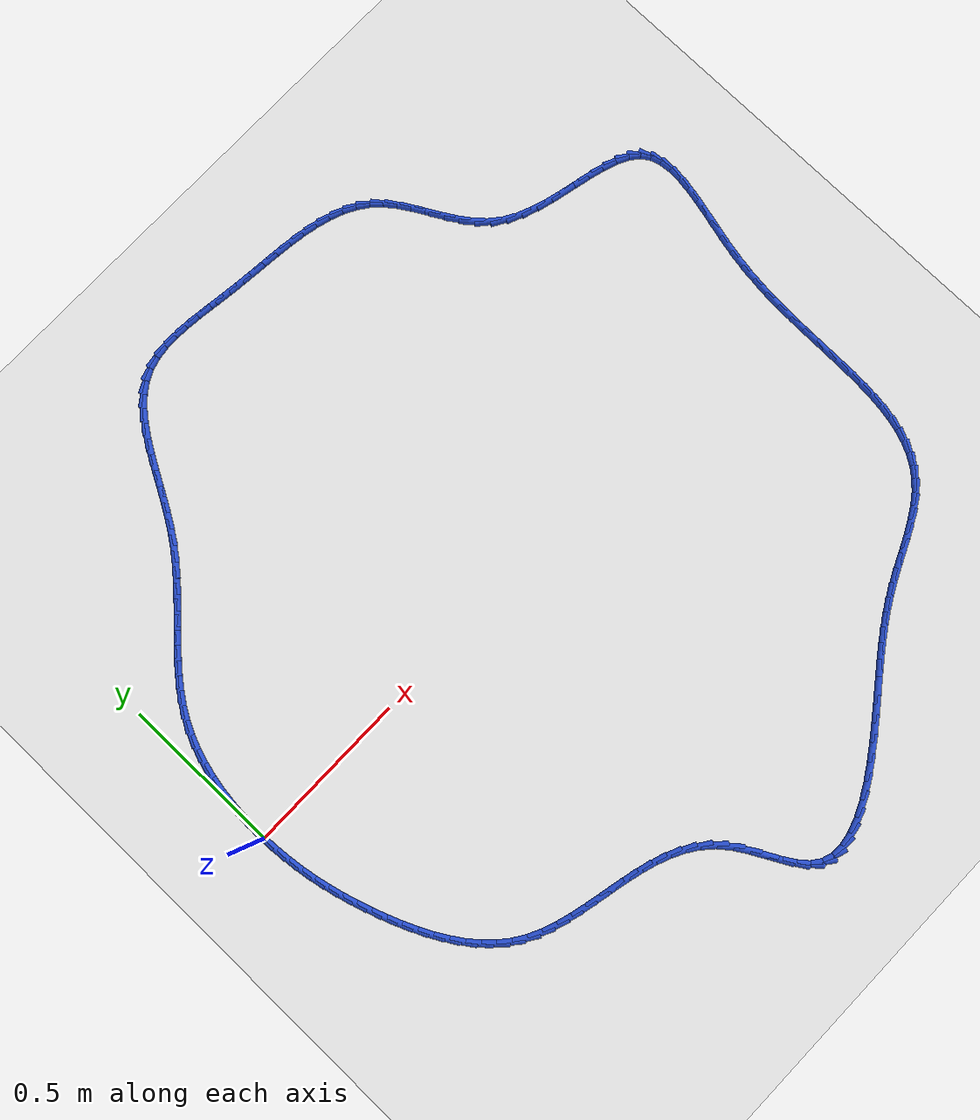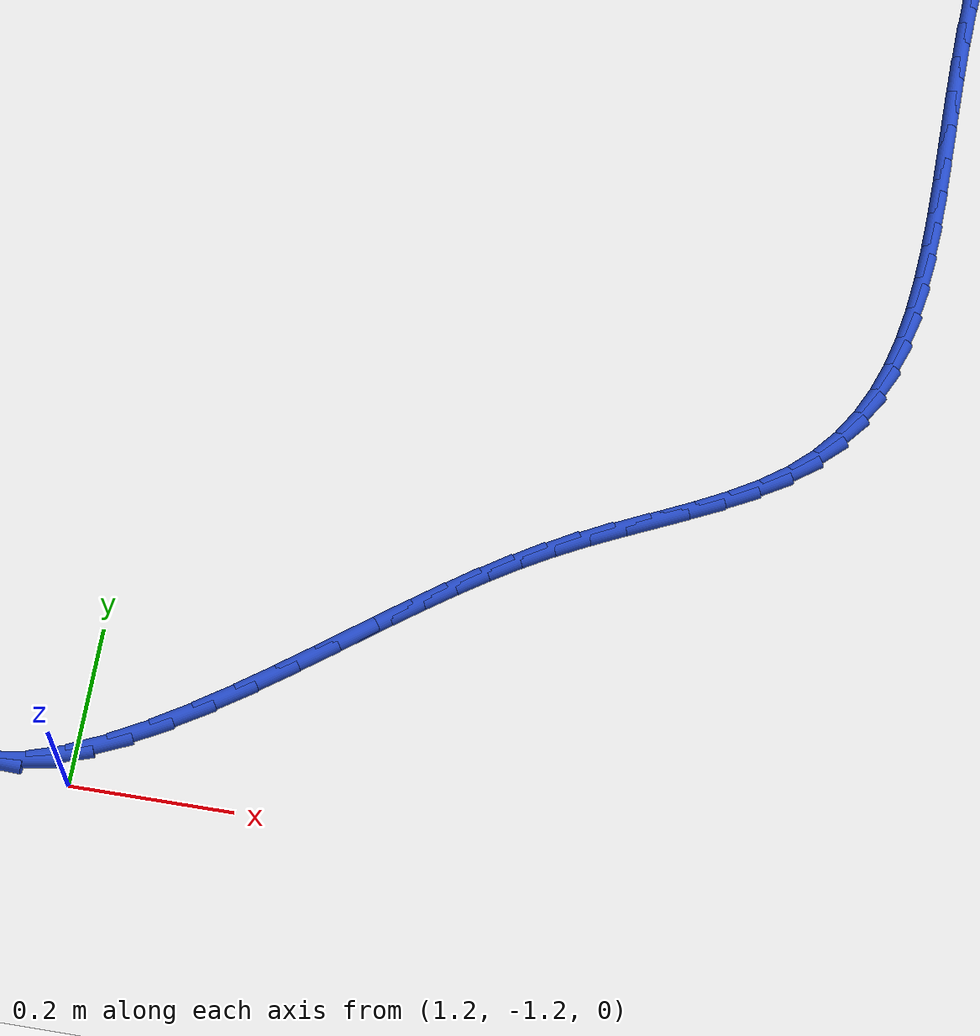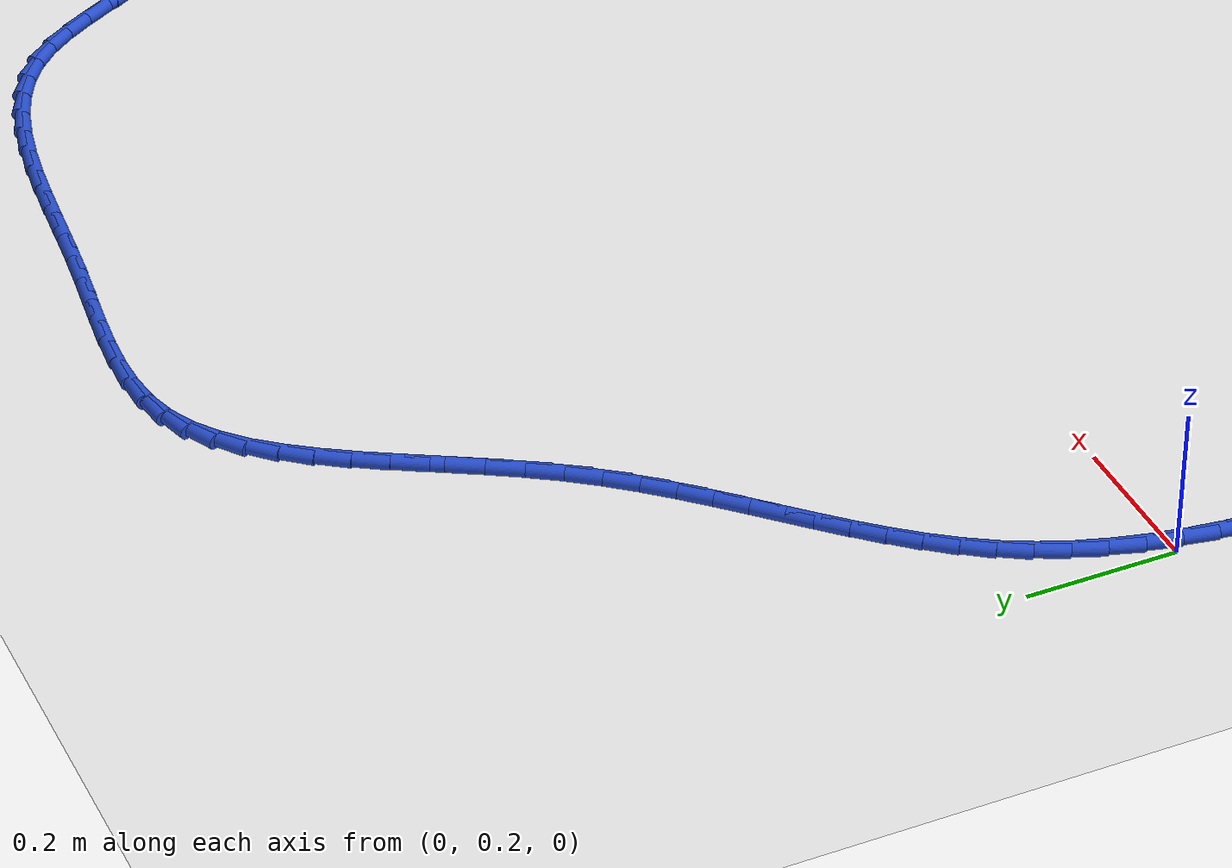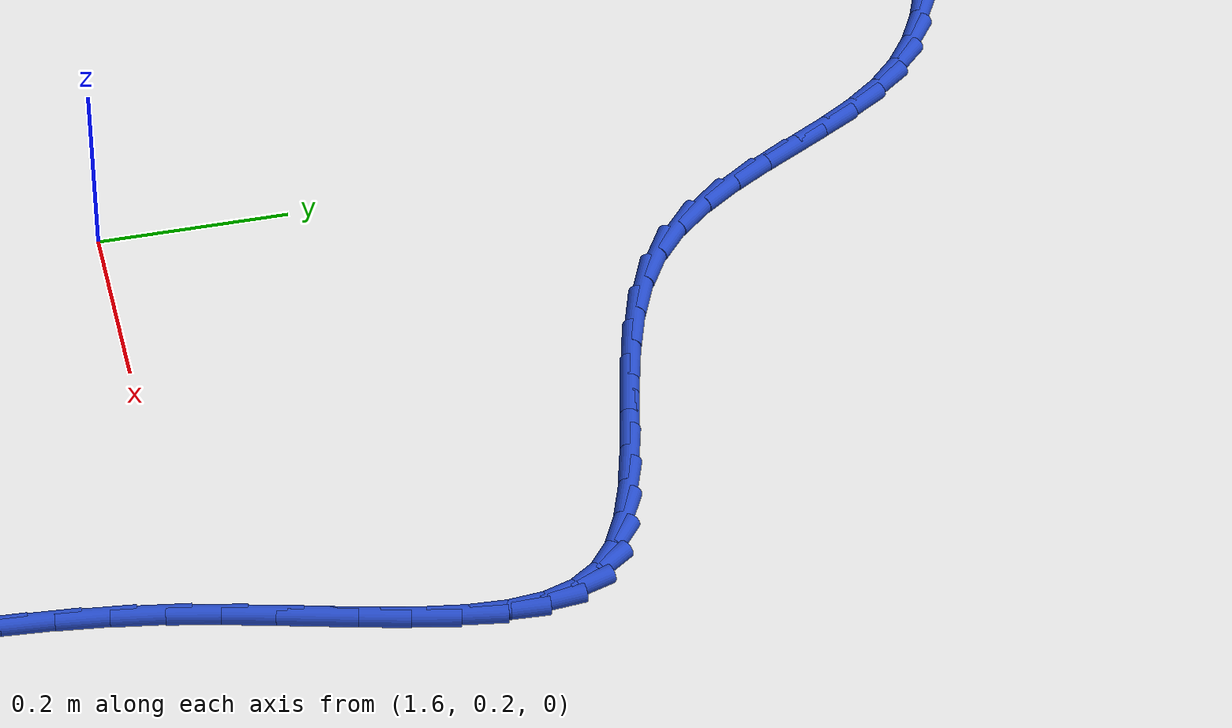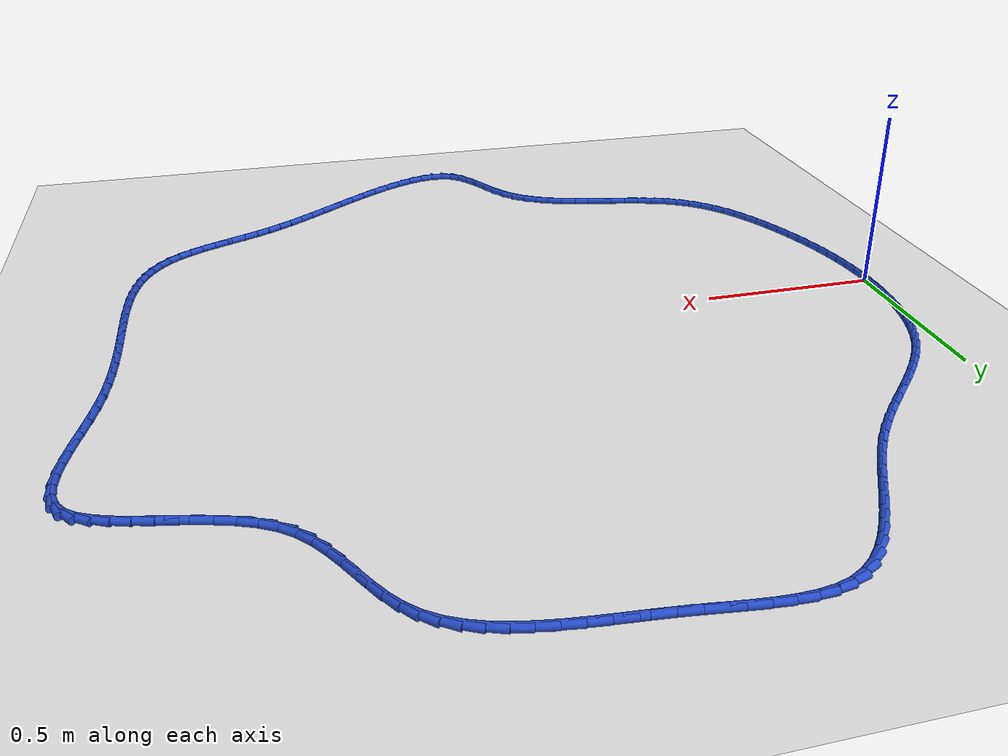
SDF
<sdf version="1.6">
 <world name="default">
  <light name="sun" type="directional">
   <pose>0 0 10 0 -0 0</pose>
   <diffuse>0.8 0.8 0.8 1</diffuse>
   <specular>0.2 0.2 0.2 1</specular>
   <attenuation>
    <range>1000</range>
    <constant>0.9</constant>
    <linear>0.01</linear>
    <quadratic>0.001</quadratic>
   </attenuation>
   <direction>-0.5 0.1 -0.9</direction>
  </light>
  <model name="ground_plane">
   <static>1</static>
   <link name="link">
    <collision name="collision">
     <geometry><plane><normal>0 0 1</normal><size>100 100</size></plane></geometry>
     <surface><friction><ode><mu>100</mu><mu2>50</mu2></ode></friction></surface>
    </collision>
    <visual name="visual">
     <cast_shadows>0</cast_shadows>
     <geometry><plane><normal>0 0 1</normal><size>100 100</size></plane></geometry>
     <material>
      <script><uri>file://media/materials/scripts/gazebo.material</uri><name>Gazebo/WhiteGlow</name></script>
     </material>
    </visual>
   </link>
  </model>
  <gravity>0 0 -9.8</gravity>
  <magnetic_field>6e-06 2.3e-05 -4.2e-05</magnetic_field>
  <atmosphere type="adiabatic"/>
  <physics name="default_physics" default="0" type="ode">
   <max_step_size>0.001</max_step_size>
   <real_time_factor>1</real_time_factor>
   <real_time_update_rate>1000</real_time_update_rate>
  </physics>
  <scene><ambient>0.4 0.4 0.4 1</ambient><background>0.7 0.7 0.7 1</background><shadows>1</shadows></scene>
  <spherical_coordinates>
   <surface_model>EARTH_WGS84</surface_model>
   <latitude_deg>0</latitude_deg>
   <longitude_deg>0</longitude_deg>
   <elevation>0</elevation>
   <heading_deg>0</heading_deg>
  </spherical_coordinates>
  <model name="line">
   <link name="link_0">
    <pose>1.734723475976807e-17 -8.326672684688674e-17 0.01 0 1.57 -1.567020768808799</pose>
    <collision name="collision">
     <geometry><cylinder><radius>0.01</radius><length>0.08</length></cylinder></geometry>
    </collision>
    <visual name="visual">
     <material>
      <script><name>Gazebo/Blue</name><uri>file://media/materials/scripts/gazebo.material</uri></script>
     </material>
     <geometry><cylinder><radius>0.01</radius><length>0.08</length></cylinder></geometry>
    </visual>
   </link>
   <link name="link_1">
    <pose>-0.0001716113039923914 0.045453013618936146 0.01 0 1.57 1.531060291461525</pose>
    <collision name="collision">
     <geometry><cylinder><radius>0.01</radius><length>0.08</length></cylinder></geometry>
    </collision>
    <visual name="visual">
     <material>
      <script><name>Gazebo/Blue</name><uri>file://media/materials/scripts/gazebo.material</uri></script>
     </material>
     <geometry><cylinder><radius>0.01</radius><length>0.08</length></cylinder></geometry>
    </visual>
   </link>
   <link name="link_2">
    <pose>0.0016462573029969371 0.09117754841347032 0.01 0 1.57 1.4847414891385309</pose>
    <collision name="collision">
     <geometry><cylinder><radius>0.01</radius><length>0.08</length></cylinder></geometry>
    </collision>
    <visual name="visual">
     <material>
      <script><name>Gazebo/Blue</name><uri>file://media/materials/scripts/gazebo.material</uri></script>
     </material>
     <geometry><cylinder><radius>0.01</radius><length>0.08</length></cylinder></geometry>
    </visual>
   </link>
   <link name="link_3">
    <pose>0.005586826914313091 0.13685583567634896 0.01 0 1.57 1.434894409735333</pose>
    <collision name="collision">
     <geometry><cylinder><radius>0.01</radius><length>0.08</length></cylinder></geometry>
    </collision>
    <visual name="visual">
     <material>
      <script><name>Gazebo/Blue</name><uri>file://media/materials/scripts/gazebo.material</uri></script>
     </material>
     <geometry><cylinder><radius>0.01</radius><length>0.08</length></cylinder></geometry>
    </visual>
   </link>
   <link name="link_4">
    <pose>0.011783318623301148 0.18217010670031847 0.01 0 1.57 1.3807547910294875</pose>
    <collision name="collision">
     <geometry><cylinder><radius>0.01</radius><length>0.08</length></cylinder></geometry>
    </collision>
    <visual name="visual">
     <material>
      <script><name>Gazebo/Blue</name><uri>file://media/materials/scripts/gazebo.material</uri></script>
     </material>
     <geometry><cylinder><radius>0.01</radius><length>0.08</length></cylinder></geometry>
    </visual>
   </link>
   <link name="link_5">
    <pose>0.020368953523306203 0.2268025927781254 0.01 0 1.57 1.3215133082210457</pose>
    <collision name="collision">
     <geometry><cylinder><radius>0.01</radius><length>0.08</length></cylinder></geometry>
    </collision>
    <visual name="visual">
     <material>
      <script><name>Gazebo/Blue</name><uri>file://media/materials/scripts/gazebo.material</uri></script>
     </material>
     <geometry><cylinder><radius>0.01</radius><length>0.08</length></cylinder></geometry>
    </visual>
   </link>
   <link name="link_6">
    <pose>0.03147695270767335 0.27043552520251624 0.01 0 1.57 1.2563290872651045</pose>
    <collision name="collision">
     <geometry><cylinder><radius>0.01</radius><length>0.08</length></cylinder></geometry>
    </collision>
    <visual name="visual">
     <material>
      <script><name>Gazebo/Blue</name><uri>file://media/materials/scripts/gazebo.material</uri></script>
     </material>
     <geometry><cylinder><radius>0.01</radius><length>0.08</length></cylinder></geometry>
    </visual>
   </link>
   <link name="link_7">
    <pose>0.045240537269747666 0.3127511352662374 0.01 0 1.57 1.1843666638737467</pose>
    <collision name="collision">
     <geometry><cylinder><radius>0.01</radius><length>0.08</length></cylinder></geometry>
    </collision>
    <visual name="visual">
     <material>
      <script><name>Gazebo/Blue</name><uri>file://media/materials/scripts/gazebo.material</uri></script>
     </material>
     <geometry><cylinder><radius>0.01</radius><length>0.08</length></cylinder></geometry>
    </visual>
   </link>
   <link name="link_8">
    <pose>0.06179292830287421 0.3534316542620354 0.01 0 1.57 1.1049145525194537</pose>
    <collision name="collision">
     <geometry><cylinder><radius>0.01</radius><length>0.08</length></cylinder></geometry>
    </collision>
    <visual name="visual">
     <material>
      <script><name>Gazebo/Blue</name><uri>file://media/materials/scripts/gazebo.material</uri></script>
     </material>
     <geometry><cylinder><radius>0.01</radius><length>0.08</length></cylinder></geometry>
    </visual>
   </link>
   <link name="link_9">
    <pose>0.0812659469510282 0.3921611291601194 0.01 0 1.57 1.0234635631427023</pose>
    <collision name="collision">
     <geometry><cylinder><radius>0.01</radius><length>0.08</length></cylinder></geometry>
    </collision>
    <visual name="visual">
     <material>
      <script><name>Gazebo/Blue</name><uri>file://media/materials/scripts/gazebo.material</uri></script>
     </material>
     <geometry><cylinder><radius>0.01</radius><length>0.08</length></cylinder></geometry>
    </visual>
   </link>
   <link name="link_10">
    <pose>0.10362177506592832 0.4288436222014961 0.01 0 1.57 0.9525425751469052</pose>
    <collision name="collision">
     <geometry><cylinder><radius>0.01</radius><length>0.08</length></cylinder></geometry>
    </collision>
    <visual name="visual">
     <material>
      <script><name>Gazebo/Blue</name><uri>file://media/materials/scripts/gazebo.material</uri></script>
     </material>
     <geometry><cylinder><radius>0.01</radius><length>0.08</length></cylinder></geometry>
    </visual>
   </link>
   <link name="link_11">
    <pose>0.12849299767693662 0.4638106693165531 0.01 0 1.57 0.8946881497671825</pose>
    <collision name="collision">
     <geometry><cylinder><radius>0.01</radius><length>0.08</length></cylinder></geometry>
    </collision>
    <visual name="visual">
     <material>
      <script><name>Gazebo/Blue</name><uri>file://media/materials/scripts/gazebo.material</uri></script>
     </material>
     <geometry><cylinder><radius>0.01</radius><length>0.08</length></cylinder></geometry>
    </visual>
   </link>
   <link name="link_12">
    <pose>0.1554743128022478 0.4974429443500773 0.01 0 1.57 0.8503619094364911</pose>
    <collision name="collision">
     <geometry><cylinder><radius>0.01</radius><length>0.08</length></cylinder></geometry>
    </collision>
    <visual name="visual">
     <material>
      <script><name>Gazebo/Blue</name><uri>file://media/materials/scripts/gazebo.material</uri></script>
     </material>
     <geometry><cylinder><radius>0.01</radius><length>0.08</length></cylinder></geometry>
    </visual>
   </link>
   <link name="link_13">
    <pose>0.1841604184600568 0.530121121146856 0.01 0 1.57 0.8195151563991074</pose>
    <collision name="collision">
     <geometry><cylinder><radius>0.01</radius><length>0.08</length></cylinder></geometry>
    </collision>
    <visual name="visual">
     <material>
      <script><name>Gazebo/Blue</name><uri>file://media/materials/scripts/gazebo.material</uri></script>
     </material>
     <geometry><cylinder><radius>0.01</radius><length>0.08</length></cylinder></geometry>
    </visual>
   </link>
   <link name="link_14">
    <pose>0.2141460126685584 0.5622258735516754 0.01 0 1.57 0.8018354752819631</pose>
    <collision name="collision">
     <geometry><cylinder><radius>0.01</radius><length>0.08</length></cylinder></geometry>
    </collision>
    <visual name="visual">
     <material>
      <script><name>Gazebo/Blue</name><uri>file://media/materials/scripts/gazebo.material</uri></script>
     </material>
     <geometry><cylinder><radius>0.01</radius><length>0.08</length></cylinder></geometry>
    </visual>
   </link>
   <link name="link_15">
    <pose>0.2450257934459474 0.594137875409323 0.01 0 1.57 0.7969192548506218</pose>
    <collision name="collision">
     <geometry><cylinder><radius>0.01</radius><length>0.08</length></cylinder></geometry>
    </collision>
    <visual name="visual">
     <material>
      <script><name>Gazebo/Blue</name><uri>file://media/materials/scripts/gazebo.material</uri></script>
     </material>
     <geometry><cylinder><radius>0.01</radius><length>0.08</length></cylinder></geometry>
    </visual>
   </link>
   <link name="link_16">
    <pose>0.27639445881041885 0.6262378005645857 0.01 0 1.57 0.8043643810675651</pose>
    <collision name="collision">
     <geometry><cylinder><radius>0.01</radius><length>0.08</length></cylinder></geometry>
    </collision>
    <visual name="visual">
     <material>
      <script><name>Gazebo/Blue</name><uri>file://media/materials/scripts/gazebo.material</uri></script>
     </material>
     <geometry><cylinder><radius>0.01</radius><length>0.08</length></cylinder></geometry>
    </visual>
   </link>
   <link name="link_17">
    <pose>0.3078467067801674 0.6589063228622505 0.01 0 1.57 0.8237936344675746</pose>
    <collision name="collision">
     <geometry><cylinder><radius>0.01</radius><length>0.08</length></cylinder></geometry>
    </collision>
    <visual name="visual">
     <material>
      <script><name>Gazebo/Blue</name><uri>file://media/materials/scripts/gazebo.material</uri></script>
     </material>
     <geometry><cylinder><radius>0.01</radius><length>0.08</length></cylinder></geometry>
    </visual>
   </link>
   <link name="link_18">
    <pose>0.3389772353733878 0.6925241161471037 0.01 0 1.57 0.854821905325866</pose>
    <collision name="collision">
     <geometry><cylinder><radius>0.01</radius><length>0.08</length></cylinder></geometry>
    </collision>
    <visual name="visual">
     <material>
      <script><name>Gazebo/Blue</name><uri>file://media/materials/scripts/gazebo.material</uri></script>
     </material>
     <geometry><cylinder><radius>0.01</radius><length>0.08</length></cylinder></geometry>
    </visual>
   </link>
   <link name="link_19">
    <pose>0.369380742608275 0.7274718542639329 0.01 0 1.57 0.8969792504650191</pose>
    <collision name="collision">
     <geometry><cylinder><radius>0.01</radius><length>0.08</length></cylinder></geometry>
    </collision>
    <visual name="visual">
     <material>
      <script><name>Gazebo/Blue</name><uri>file://media/materials/scripts/gazebo.material</uri></script>
     </material>
     <geometry><cylinder><radius>0.01</radius><length>0.08</length></cylinder></geometry>
    </visual>
   </link>
   <link name="link_20">
    <pose>0.39865192650302383 0.7641302110575249 0.01 0 1.57 0.9495236927692865</pose>
    <collision name="collision">
     <geometry><cylinder><radius>0.01</radius><length>0.08</length></cylinder></geometry>
    </collision>
    <visual name="visual">
     <material>
      <script><name>Gazebo/Blue</name><uri>file://media/materials/scripts/gazebo.material</uri></script>
     </material>
     <geometry><cylinder><radius>0.01</radius><length>0.08</length></cylinder></geometry>
    </visual>
   </link>
   <link name="link_21">
    <pose>0.42638784451346956 0.8028766176585421 0.01 0 1.57 1.002469114185338</pose>
    <collision name="collision">
     <geometry><cylinder><radius>0.01</radius><length>0.08</length></cylinder></geometry>
    </collision>
    <visual name="visual">
     <material>
      <script><name>Gazebo/Blue</name><uri>file://media/materials/scripts/gazebo.material</uri></script>
     </material>
     <geometry><cylinder><radius>0.01</radius><length>0.08</length></cylinder></geometry>
    </visual>
   </link>
   <link name="link_22">
    <pose>0.452462841278048 0.8437074130898607 0.01 0 1.57 1.0388543029994732</pose>
    <collision name="collision">
     <geometry><cylinder><radius>0.01</radius><length>0.08</length></cylinder></geometry>
    </collision>
    <visual name="visual">
     <material>
      <script><name>Gazebo/Blue</name><uri>file://media/materials/scripts/gazebo.material</uri></script>
     </material>
     <geometry><cylinder><radius>0.01</radius><length>0.08</length></cylinder></geometry>
    </visual>
   </link>
   <link name="link_23">
    <pose>0.47728543689604785 0.8858847875745639 0.01 0 1.57 1.0580643525818694</pose>
    <collision name="collision">
     <geometry><cylinder><radius>0.01</radius><length>0.08</length></cylinder></geometry>
    </collision>
    <visual name="visual">
     <material>
      <script><name>Gazebo/Blue</name><uri>file://media/materials/scripts/gazebo.material</uri></script>
     </material>
     <geometry><cylinder><radius>0.01</radius><length>0.08</length></cylinder></geometry>
    </visual>
   </link>
   <link name="link_24">
    <pose>0.5013249210161304 0.9285874121645922 0.01 0 1.57 1.0607030882720003</pose>
    <collision name="collision">
     <geometry><cylinder><radius>0.01</radius><length>0.08</length></cylinder></geometry>
    </collision>
    <visual name="visual">
     <material>
      <script><name>Gazebo/Blue</name><uri>file://media/materials/scripts/gazebo.material</uri></script>
     </material>
     <geometry><cylinder><radius>0.01</radius><length>0.08</length></cylinder></geometry>
    </visual>
   </link>
   <link name="link_25">
    <pose>0.5250505832869565 0.9709939579118848 0.01 0 1.57 1.046419817949653</pose>
    <collision name="collision">
     <geometry><cylinder><radius>0.01</radius><length>0.08</length></cylinder></geometry>
    </collision>
    <visual name="visual">
     <material>
      <script><name>Gazebo/Blue</name><uri>file://media/materials/scripts/gazebo.material</uri></script>
     </material>
     <geometry><cylinder><radius>0.01</radius><length>0.08</length></cylinder></geometry>
    </visual>
   </link>
   <link name="link_26">
    <pose>0.5489317133571877 1.0122830958683822 0.01 0 1.57 1.0138088401947063</pose>
    <collision name="collision">
     <geometry><cylinder><radius>0.01</radius><length>0.08</length></cylinder></geometry>
    </collision>
    <visual name="visual">
     <material>
      <script><name>Gazebo/Blue</name><uri>file://media/materials/scripts/gazebo.material</uri></script>
     </material>
     <geometry><cylinder><radius>0.01</radius><length>0.08</length></cylinder></geometry>
    </visual>
   </link>
   <link name="link_27">
    <pose>0.5734376008754849 1.0516334970860242 0.01 0 1.57 0.9603143577371854</pose>
    <collision name="collision">
     <geometry><cylinder><radius>0.01</radius><length>0.08</length></cylinder></geometry>
    </collision>
    <visual name="visual">
     <material>
      <script><name>Gazebo/Blue</name><uri>file://media/materials/scripts/gazebo.material</uri></script>
     </material>
     <geometry><cylinder><radius>0.01</radius><length>0.08</length></cylinder></geometry>
    </visual>
   </link>
   <link name="link_28">
    <pose>0.5990375354905093 1.0882238326167508 0.01 0 1.57 0.8822432423449317</pose>
    <collision name="collision">
     <geometry><cylinder><radius>0.01</radius><length>0.08</length></cylinder></geometry>
    </collision>
    <visual name="visual">
     <material>
      <script><name>Gazebo/Blue</name><uri>file://media/materials/scripts/gazebo.material</uri></script>
     </material>
     <geometry><cylinder><radius>0.01</radius><length>0.08</length></cylinder></geometry>
    </visual>
   </link>
   <link name="link_29">
    <pose>0.6262008068509223 1.1212327735125018 0.01 0 1.57 0.7751968068318239</pose>
    <collision name="collision">
     <geometry><cylinder><radius>0.01</radius><length>0.08</length></cylinder></geometry>
    </collision>
    <visual name="visual">
     <material>
      <script><name>Gazebo/Blue</name><uri>file://media/materials/scripts/gazebo.material</uri></script>
     </material>
     <geometry><cylinder><radius>0.01</radius><length>0.08</length></cylinder></geometry>
    </visual>
   </link>
   <link name="link_30">
    <pose>0.6553967046053845 1.149838990825217 0.01 0 1.57 0.6355557080730524</pose>
    <collision name="collision">
     <geometry><cylinder><radius>0.01</radius><length>0.08</length></cylinder></geometry>
    </collision>
    <visual name="visual">
     <material>
      <script><name>Gazebo/Blue</name><uri>file://media/materials/scripts/gazebo.material</uri></script>
     </material>
     <geometry><cylinder><radius>0.01</radius><length>0.08</length></cylinder></geometry>
    </visual>
   </link>
   <link name="link_31">
    <pose>0.6870945184025575 1.1732211556068364 0.01 0 1.57 0.463774441154091</pose>
    <collision name="collision">
     <geometry><cylinder><radius>0.01</radius><length>0.08</length></cylinder></geometry>
    </collision>
    <visual name="visual">
     <material>
      <script><name>Gazebo/Blue</name><uri>file://media/materials/scripts/gazebo.material</uri></script>
     </material>
     <geometry><cylinder><radius>0.01</radius><length>0.08</length></cylinder></geometry>
    </visual>
   </link>
   <link name="link_32">
    <pose>0.7217623127674697 1.1905605493766551 0.01 0 1.57 0.2828826860031082</pose>
    <collision name="collision">
     <geometry><cylinder><radius>0.01</radius><length>0.08</length></cylinder></geometry>
    </collision>
    <visual name="visual">
     <material>
      <script><name>Gazebo/Blue</name><uri>file://media/materials/scripts/gazebo.material</uri></script>
     </material>
     <geometry><cylinder><radius>0.01</radius><length>0.08</length></cylinder></geometry>
    </visual>
   </link>
   <link name="link_33">
    <pose>0.7596209358070171 1.2015652171349809 0.01 0 1.57 0.13521582477753552</pose>
    <collision name="collision">
     <geometry><cylinder><radius>0.01</radius><length>0.08</length></cylinder></geometry>
    </collision>
    <visual name="visual">
     <material>
      <script><name>Gazebo/Blue</name><uri>file://media/materials/scripts/gazebo.material</uri></script>
     </material>
     <geometry><cylinder><radius>0.01</radius><length>0.08</length></cylinder></geometry>
    </visual>
   </link>
   <link name="link_34">
    <pose>0.8003456835745526 1.207105654584084 0.01 0 1.57 0.025508180863463757</pose>
    <collision name="collision">
     <geometry><cylinder><radius>0.01</radius><length>0.08</length></cylinder></geometry>
    </collision>
    <visual name="visual">
     <material>
      <script><name>Gazebo/Blue</name><uri>file://media/materials/scripts/gazebo.material</uri></script>
     </material>
     <geometry><cylinder><radius>0.01</radius><length>0.08</length></cylinder></geometry>
    </visual>
   </link>
   <link name="link_35">
    <pose>0.8435389594867071 1.2082076755048277 0.01 0 1.57 -0.05100228534012227</pose>
    <collision name="collision">
     <geometry><cylinder><radius>0.01</radius><length>0.08</length></cylinder></geometry>
    </collision>
    <visual name="visual">
     <material>
      <script><name>Gazebo/Blue</name><uri>file://media/materials/scripts/gazebo.material</uri></script>
     </material>
     <geometry><cylinder><radius>0.01</radius><length>0.08</length></cylinder></geometry>
    </visual>
   </link>
   <link name="link_36">
    <pose>0.8888031669601106 1.2058970936780748 0.01 0 1.57 -0.09974493926160515</pose>
    <collision name="collision">
     <geometry><cylinder><radius>0.01</radius><length>0.08</length></cylinder></geometry>
    </collision>
    <visual name="visual">
     <material>
      <script><name>Gazebo/Blue</name><uri>file://media/materials/scripts/gazebo.material</uri></script>
     </material>
     <geometry><cylinder><radius>0.01</radius><length>0.08</length></cylinder></geometry>
    </visual>
   </link>
   <link name="link_37">
    <pose>0.9357407094113933 1.2011997228846887 0.01 0 1.57 -0.12500203350022768</pose>
    <collision name="collision">
     <geometry><cylinder><radius>0.01</radius><length>0.08</length></cylinder></geometry>
    </collision>
    <visual name="visual">
     <material>
      <script><name>Gazebo/Blue</name><uri>file://media/materials/scripts/gazebo.material</uri></script>
     </material>
     <geometry><cylinder><radius>0.01</radius><length>0.08</length></cylinder></geometry>
    </visual>
   </link>
   <link name="link_38">
    <pose>0.9839539902571846 1.195141376905531 0.01 0 1.57 -0.1295078133055338</pose>
    <collision name="collision">
     <geometry><cylinder><radius>0.01</radius><length>0.08</length></cylinder></geometry>
    </collision>
    <visual name="visual">
     <material>
      <script><name>Gazebo/Blue</name><uri>file://media/materials/scripts/gazebo.material</uri></script>
     </material>
     <geometry><cylinder><radius>0.01</radius><length>0.08</length></cylinder></geometry>
    </visual>
   </link>
   <link name="link_39">
    <pose>1.033045412914115 1.1887478695214653 0.01 0 1.57 -0.11509646648038017</pose>
    <collision name="collision">
     <geometry><cylinder><radius>0.01</radius><length>0.08</length></cylinder></geometry>
    </collision>
    <visual name="visual">
     <material>
      <script><name>Gazebo/Blue</name><uri>file://media/materials/scripts/gazebo.material</uri></script>
     </material>
     <geometry><cylinder><radius>0.01</radius><length>0.08</length></cylinder></geometry>
    </visual>
   </link>
   <link name="link_40">
    <pose>1.0826175750169273 1.1830169602899379 0.01 0 1.57 -0.09677783158054479</pose>
    <collision name="collision">
     <geometry><cylinder><radius>0.01</radius><length>0.08</length></cylinder></geometry>
    </collision>
    <visual name="visual">
     <material>
      <script><name>Gazebo/Blue</name><uri>file://media/materials/scripts/gazebo.material</uri></script>
     </material>
     <geometry><cylinder><radius>0.01</radius><length>0.08</length></cylinder></geometry>
    </visual>
   </link>
   <link name="link_41">
    <pose>1.132278270318947 1.178195845038016 0.01 0 1.57 -0.0904752718898803</pose>
    <collision name="collision">
     <geometry><cylinder><radius>0.01</radius><length>0.08</length></cylinder></geometry>
    </collision>
    <visual name="visual">
     <material>
      <script><name>Gazebo/Blue</name><uri>file://media/materials/scripts/gazebo.material</uri></script>
     </material>
     <geometry><cylinder><radius>0.01</radius><length>0.08</length></cylinder></geometry>
    </visual>
   </link>
   <link name="link_42">
    <pose>1.1816409292481973 1.1737175188533193 0.01 0 1.57 -0.09713606989486073</pose>
    <collision name="collision">
     <geometry><cylinder><radius>0.01</radius><length>0.08</length></cylinder></geometry>
    </collision>
    <visual name="visual">
     <material>
      <script><name>Gazebo/Blue</name><uri>file://media/materials/scripts/gazebo.material</uri></script>
     </material>
     <geometry><cylinder><radius>0.01</radius><length>0.08</length></cylinder></geometry>
    </visual>
   </link>
   <link name="link_43">
    <pose>1.2303192647450185 1.1689741687676656 0.01 0 1.57 -0.11742526869978262</pose>
    <collision name="collision">
     <geometry><cylinder><radius>0.01</radius><length>0.08</length></cylinder></geometry>
    </collision>
    <visual name="visual">
     <material>
      <script><name>Gazebo/Blue</name><uri>file://media/materials/scripts/gazebo.material</uri></script>
     </material>
     <geometry><cylinder><radius>0.01</radius><length>0.08</length></cylinder></geometry>
    </visual>
   </link>
   <link name="link_44">
    <pose>1.2779269897497514 1.1633579818128734 0.01 0 1.57 -0.15257967717023743</pose>
    <collision name="collision">
     <geometry><cylinder><radius>0.01</radius><length>0.08</length></cylinder></geometry>
    </collision>
    <visual name="visual">
     <material>
      <script><name>Gazebo/Blue</name><uri>file://media/materials/scripts/gazebo.material</uri></script>
     </material>
     <geometry><cylinder><radius>0.01</radius><length>0.08</length></cylinder></geometry>
    </visual>
   </link>
   <link name="link_45">
    <pose>1.324077817202735 1.1562611450207612 0.01 0 1.57 -0.2044118736837749</pose>
    <collision name="collision">
     <geometry><cylinder><radius>0.01</radius><length>0.08</length></cylinder></geometry>
    </collision>
    <visual name="visual">
     <material>
      <script><name>Gazebo/Blue</name><uri>file://media/materials/scripts/gazebo.material</uri></script>
     </material>
     <geometry><cylinder><radius>0.01</radius><length>0.08</length></cylinder></geometry>
    </visual>
   </link>
   <link name="link_46">
    <pose>1.3683854600443102 1.1470758454231471 0.01 0 1.57 -0.27520421583713045</pose>
    <collision name="collision">
     <geometry><cylinder><radius>0.01</radius><length>0.08</length></cylinder></geometry>
    </collision>
    <visual name="visual">
     <material>
      <script><name>Gazebo/Blue</name><uri>file://media/materials/scripts/gazebo.material</uri></script>
     </material>
     <geometry><cylinder><radius>0.01</radius><length>0.08</length></cylinder></geometry>
    </visual>
   </link>
   <link name="link_47">
    <pose>1.4104636312148158 1.1351942700518503 0.01 0 1.57 -0.36734629845980316</pose>
    <collision name="collision">
     <geometry><cylinder><radius>0.01</radius><length>0.08</length></cylinder></geometry>
    </collision>
    <visual name="visual">
     <material>
      <script><name>Gazebo/Blue</name><uri>file://media/materials/scripts/gazebo.material</uri></script>
     </material>
     <geometry><cylinder><radius>0.01</radius><length>0.08</length></cylinder></geometry>
    </visual>
   </link>
   <link name="link_48">
    <pose>1.4499260436545929 1.1200086059386878 0.01 0 1.57 -0.48249776748284084</pose>
    <collision name="collision">
     <geometry><cylinder><radius>0.01</radius><length>0.08</length></cylinder></geometry>
    </collision>
    <visual name="visual">
     <material>
      <script><name>Gazebo/Blue</name><uri>file://media/materials/scripts/gazebo.material</uri></script>
     </material>
     <geometry><cylinder><radius>0.01</radius><length>0.08</length></cylinder></geometry>
    </visual>
   </link>
   <link name="link_49">
    <pose>1.4863864103039797 1.100911040115479 0.01 0 1.57 -0.6201373391399486</pose>
    <collision name="collision">
     <geometry><cylinder><radius>0.01</radius><length>0.08</length></cylinder></geometry>
    </collision>
    <visual name="visual">
     <material>
      <script><name>Gazebo/Blue</name><uri>file://media/materials/scripts/gazebo.material</uri></script>
     </material>
     <geometry><cylinder><radius>0.01</radius><length>0.08</length></cylinder></geometry>
    </visual>
   </link>
   <link name="link_50">
    <pose>1.5194584441033183 1.0772937596140424 0.01 0 1.57 -0.7754929869266919</pose>
    <collision name="collision">
     <geometry><cylinder><radius>0.01</radius><length>0.08</length></cylinder></geometry>
    </collision>
    <visual name="visual">
     <material>
      <script><name>Gazebo/Blue</name><uri>file://media/materials/scripts/gazebo.material</uri></script>
     </material>
     <geometry><cylinder><radius>0.01</radius><length>0.08</length></cylinder></geometry>
    </visual>
   </link>
   <link name="link_51">
    <pose>1.548765729269281 1.0485613863096712 0.01 0 1.57 -0.9178784529399259</pose>
    <collision name="collision">
     <geometry><cylinder><radius>0.01</radius><length>0.08</length></cylinder></geometry>
    </collision>
    <visual name="visual">
     <material>
      <script><name>Gazebo/Blue</name><uri>file://media/materials/scripts/gazebo.material</uri></script>
     </material>
     <geometry><cylinder><radius>0.01</radius><length>0.08</length></cylinder></geometry>
    </visual>
   </link>
   <link name="link_52">
    <pose>1.5745310089407965 1.0148733023704164 0.01 0 1.57 -1.0110367568539764</pose>
    <collision name="collision">
     <geometry><cylinder><radius>0.01</radius><length>0.08</length></cylinder></geometry>
    </collision>
    <visual name="visual">
     <material>
      <script><name>Gazebo/Blue</name><uri>file://media/materials/scripts/gazebo.material</uri></script>
     </material>
     <geometry><cylinder><radius>0.01</radius><length>0.08</length></cylinder></geometry>
    </visual>
   </link>
   <link name="link_53">
    <pose>1.5979097016994699 0.9775637809056317 0.01 0 1.57 -1.05817097421774</pose>
    <collision name="collision">
     <geometry><cylinder><radius>0.01</radius><length>0.08</length></cylinder></geometry>
    </collision>
    <visual name="visual">
     <material>
      <script><name>Gazebo/Blue</name><uri>file://media/materials/scripts/gazebo.material</uri></script>
     </material>
     <geometry><cylinder><radius>0.01</radius><length>0.08</length></cylinder></geometry>
    </visual>
   </link>
   <link name="link_54">
    <pose>1.6201379231485131 0.9380687490356378 0.01 0 1.57 -1.0645384903842996</pose>
    <collision name="collision">
     <geometry><cylinder><radius>0.01</radius><length>0.08</length></cylinder></geometry>
    </collision>
    <visual name="visual">
     <material>
      <script><name>Gazebo/Blue</name><uri>file://media/materials/scripts/gazebo.material</uri></script>
     </material>
     <geometry><cylinder><radius>0.01</radius><length>0.08</length></cylinder></geometry>
    </visual>
   </link>
   <link name="link_55">
    <pose>1.6424517888911372 0.897824133880754 0.01 0 1.57 -1.0322253135391355</pose>
    <collision name="collision">
     <geometry><cylinder><radius>0.01</radius><length>0.08</length></cylinder></geometry>
    </collision>
    <visual name="visual">
     <material>
      <script><name>Gazebo/Blue</name><uri>file://media/materials/scripts/gazebo.material</uri></script>
     </material>
     <geometry><cylinder><radius>0.01</radius><length>0.08</length></cylinder></geometry>
    </visual>
   </link>
   <link name="link_56">
    <pose>1.6660874145305553 0.8582658625613009 0.01 0 1.57 -0.9602801312883518</pose>
    <collision name="collision">
     <geometry><cylinder><radius>0.01</radius><length>0.08</length></cylinder></geometry>
    </collision>
    <visual name="visual">
     <material>
      <script><name>Gazebo/Blue</name><uri>file://media/materials/scripts/gazebo.material</uri></script>
     </material>
     <geometry><cylinder><radius>0.01</radius><length>0.08</length></cylinder></geometry>
    </visual>
   </link>
   <link name="link_57">
    <pose>1.69228091566998 0.8208298621975995 0.01 0 1.57 -0.8462372940151093</pose>
    <collision name="collision">
     <geometry><cylinder><radius>0.01</radius><length>0.08</length></cylinder></geometry>
    </collision>
    <visual name="visual">
     <material>
      <script><name>Gazebo/Blue</name><uri>file://media/materials/scripts/gazebo.material</uri></script>
     </material>
     <geometry><cylinder><radius>0.01</radius><length>0.08</length></cylinder></geometry>
    </visual>
   </link>
   <link name="link_58">
    <pose>1.722268407912623 0.7869520599099691 0.01 0 1.57 -0.6898736377977203</pose>
    <collision name="collision">
     <geometry><cylinder><radius>0.01</radius><length>0.08</length></cylinder></geometry>
    </collision>
    <visual name="visual">
     <material>
      <script><name>Gazebo/Blue</name><uri>file://media/materials/scripts/gazebo.material</uri></script>
     </material>
     <geometry><cylinder><radius>0.01</radius><length>0.08</length></cylinder></geometry>
    </visual>
   </link>
   <link name="link_59">
    <pose>1.757280322150871 0.7580629000448772 0.01 0 1.57 -0.5216028524493134</pose>
    <collision name="collision">
     <geometry><cylinder><radius>0.01</radius><length>0.08</length></cylinder></geometry>
    </collision>
    <visual name="visual">
     <material>
      <script><name>Gazebo/Blue</name><uri>file://media/materials/scripts/gazebo.material</uri></script>
     </material>
     <geometry><cylinder><radius>0.01</radius><length>0.08</length></cylinder></geometry>
    </visual>
   </link>
   <link name="link_60">
    <pose>1.7977378138464941 0.7348122992653512 0.01 0 1.57 -0.3934129438212262</pose>
    <collision name="collision">
     <geometry><cylinder><radius>0.01</radius><length>0.08</length></cylinder></geometry>
    </collision>
    <visual name="visual">
     <material>
      <script><name>Gazebo/Blue</name><uri>file://media/materials/scripts/gazebo.material</uri></script>
     </material>
     <geometry><cylinder><radius>0.01</radius><length>0.08</length></cylinder></geometry>
    </visual>
   </link>
   <link name="link_61">
    <pose>1.8424203519500384 0.7162668050611308 0.01 0 1.57 -0.3052897751053289</pose>
    <collision name="collision">
     <geometry><cylinder><radius>0.01</radius><length>0.08</length></cylinder></geometry>
    </collision>
    <visual name="visual">
     <material>
      <script><name>Gazebo/Blue</name><uri>file://media/materials/scripts/gazebo.material</uri></script>
     </material>
     <geometry><cylinder><radius>0.01</radius><length>0.08</length></cylinder></geometry>
    </visual>
   </link>
   <link name="link_62">
    <pose>1.8899086420144058 0.7013012621611341 0.01 0 1.57 -0.25059487909021544</pose>
    <collision name="collision">
     <geometry><cylinder><radius>0.01</radius><length>0.08</length></cylinder></geometry>
    </collision>
    <visual name="visual">
     <material>
      <script><name>Gazebo/Blue</name><uri>file://media/materials/scripts/gazebo.material</uri></script>
     </material>
     <geometry><cylinder><radius>0.01</radius><length>0.08</length></cylinder></geometry>
    </visual>
   </link>
   <link name="link_63">
    <pose>1.9387833895924984 0.6887905152942778 0.01 0 1.57 -0.22504660852469163</pose>
    <collision name="collision">
     <geometry><cylinder><radius>0.01</radius><length>0.08</length></cylinder></geometry>
    </collision>
    <visual name="visual">
     <material>
      <script><name>Gazebo/Blue</name><uri>file://media/materials/scripts/gazebo.material</uri></script>
     </material>
     <geometry><cylinder><radius>0.01</radius><length>0.08</length></cylinder></geometry>
    </visual>
   </link>
   <link name="link_64">
    <pose>1.9876253002372177 0.6776094091894794 0.01 0 1.57 -0.22761045439036845</pose>
    <collision name="collision">
     <geometry><cylinder><radius>0.01</radius><length>0.08</length></cylinder></geometry>
    </collision>
    <visual name="visual">
     <material>
      <script><name>Gazebo/Blue</name><uri>file://media/materials/scripts/gazebo.material</uri></script>
     </material>
     <geometry><cylinder><radius>0.01</radius><length>0.08</length></cylinder></geometry>
    </visual>
   </link>
   <link name="link_65">
    <pose>2.035015079501467 0.666632788575657 0.01 0 1.57 -0.26114189593670845</pose>
    <collision name="collision">
     <geometry><cylinder><radius>0.01</radius><length>0.08</length></cylinder></geometry>
    </collision>
    <visual name="visual">
     <material>
      <script><name>Gazebo/Blue</name><uri>file://media/materials/scripts/gazebo.material</uri></script>
     </material>
     <geometry><cylinder><radius>0.01</radius><length>0.08</length></cylinder></geometry>
    </visual>
   </link>
   <link name="link_66">
    <pose>2.079533432938148 0.654735498181727 0.01 0 1.57 -0.33364749427212603</pose>
    <collision name="collision">
     <geometry><cylinder><radius>0.01</radius><length>0.08</length></cylinder></geometry>
    </collision>
    <visual name="visual">
     <material>
      <script><name>Gazebo/Blue</name><uri>file://media/materials/scripts/gazebo.material</uri></script>
     </material>
     <geometry><cylinder><radius>0.01</radius><length>0.08</length></cylinder></geometry>
    </visual>
   </link>
   <link name="link_67">
    <pose>2.119761066100162 0.6407923827366071 0.01 0 1.57 -0.4602880261965378</pose>
    <collision name="collision">
     <geometry><cylinder><radius>0.01</radius><length>0.08</length></cylinder></geometry>
    </collision>
    <visual name="visual">
     <material>
      <script><name>Gazebo/Blue</name><uri>file://media/materials/scripts/gazebo.material</uri></script>
     </material>
     <geometry><cylinder><radius>0.01</radius><length>0.08</length></cylinder></geometry>
    </visual>
   </link>
   <link name="link_68">
    <pose>2.1542786845404116 0.6236782869692146 0.01 0 1.57 -0.6635002776766473</pose>
    <collision name="collision">
     <geometry><cylinder><radius>0.01</radius><length>0.08</length></cylinder></geometry>
    </collision>
    <visual name="visual">
     <material>
      <script><name>Gazebo/Blue</name><uri>file://media/materials/scripts/gazebo.material</uri></script>
     </material>
     <geometry><cylinder><radius>0.01</radius><length>0.08</length></cylinder></geometry>
    </visual>
   </link>
   <link name="link_69">
    <pose>2.181666993811799 0.6022680556084669 0.01 0 1.57 -0.9549746863354363</pose>
    <collision name="collision">
     <geometry><cylinder><radius>0.01</radius><length>0.08</length></cylinder></geometry>
    </collision>
    <visual name="visual">
     <material>
      <script><name>Gazebo/Blue</name><uri>file://media/materials/scripts/gazebo.material</uri></script>
     </material>
     <geometry><cylinder><radius>0.01</radius><length>0.08</length></cylinder></geometry>
    </visual>
   </link>
   <link name="link_70">
    <pose>2.2006069677996667 0.5755023066717475 0.01 0 1.57 -1.2522200234440308</pose>
    <collision name="collision">
     <geometry><cylinder><radius>0.01</radius><length>0.08</length></cylinder></geometry>
    </collision>
    <visual name="visual">
     <material>
      <script><name>Gazebo/Blue</name><uri>file://media/materials/scripts/gazebo.material</uri></script>
     </material>
     <geometry><cylinder><radius>0.01</radius><length>0.08</length></cylinder></geometry>
    </visual>
   </link>
   <link name="link_71">
    <pose>2.2112353338651984 0.5432765927103242 0.01 0 1.57 -1.47527466905708</pose>
    <collision name="collision">
     <geometry><cylinder><radius>0.01</radius><length>0.08</length></cylinder></geometry>
    </collision>
    <visual name="visual">
     <material>
      <script><name>Gazebo/Blue</name><uri>file://media/materials/scripts/gazebo.material</uri></script>
     </material>
     <geometry><cylinder><radius>0.01</radius><length>0.08</length></cylinder></geometry>
    </visual>
   </link>
   <link name="link_72">
    <pose>2.2147871006642457 0.5062069088185212 0.01 0 1.57 1.5160343552844908</pose>
    <collision name="collision">
     <geometry><cylinder><radius>0.01</radius><length>0.08</length></cylinder></geometry>
    </collision>
    <visual name="visual">
     <material>
      <script><name>Gazebo/Blue</name><uri>file://media/materials/scripts/gazebo.material</uri></script>
     </material>
     <geometry><cylinder><radius>0.01</radius><length>0.08</length></cylinder></geometry>
    </visual>
   </link>
   <link name="link_73">
    <pose>2.2125242665503366 0.4649269545954397 0.01 0 1.57 1.4200109994187369</pose>
    <collision name="collision">
     <geometry><cylinder><radius>0.01</radius><length>0.08</length></cylinder></geometry>
    </collision>
    <visual name="visual">
     <material>
      <script><name>Gazebo/Blue</name><uri>file://media/materials/scripts/gazebo.material</uri></script>
     </material>
     <geometry><cylinder><radius>0.01</radius><length>0.08</length></cylinder></geometry>
    </visual>
   </link>
   <link name="link_74">
    <pose>2.2057088298769982 0.4200704296401827 0.01 0 1.57 1.362438640082577</pose>
    <collision name="collision">
     <geometry><cylinder><radius>0.01</radius><length>0.08</length></cylinder></geometry>
    </collision>
    <visual name="visual">
     <material>
      <script><name>Gazebo/Blue</name><uri>file://media/materials/scripts/gazebo.material</uri></script>
     </material>
     <geometry><cylinder><radius>0.01</radius><length>0.08</length></cylinder></geometry>
    </visual>
   </link>
   <link name="link_75">
    <pose>2.195602788997757 0.3722710335518518 0.01 0 1.57 1.333203278508561</pose>
    <collision name="collision">
     <geometry><cylinder><radius>0.01</radius><length>0.08</length></cylinder></geometry>
    </collision>
    <visual name="visual">
     <material>
      <script><name>Gazebo/Blue</name><uri>file://media/materials/scripts/gazebo.material</uri></script>
     </material>
     <geometry><cylinder><radius>0.01</radius><length>0.08</length></cylinder></geometry>
    </visual>
   </link>
   <link name="link_76">
    <pose>2.1834681422661406 0.3221624659295486 0.01 0 1.57 1.326631264381721</pose>
    <collision name="collision">
     <geometry><cylinder><radius>0.01</radius><length>0.08</length></cylinder></geometry>
    </collision>
    <visual name="visual">
     <material>
      <script><name>Gazebo/Blue</name><uri>file://media/materials/scripts/gazebo.material</uri></script>
     </material>
     <geometry><cylinder><radius>0.01</radius><length>0.08</length></cylinder></geometry>
    </visual>
   </link>
   <link name="link_77">
    <pose>2.1705668880356765 0.27037842637237625 0.01 0 1.57 1.340131518238617</pose>
    <collision name="collision">
     <geometry><cylinder><radius>0.01</radius><length>0.08</length></cylinder></geometry>
    </collision>
    <visual name="visual">
     <material>
      <script><name>Gazebo/Blue</name><uri>file://media/materials/scripts/gazebo.material</uri></script>
     </material>
     <geometry><cylinder><radius>0.01</radius><length>0.08</length></cylinder></geometry>
    </visual>
   </link>
   <link name="link_78">
    <pose>2.1581610246598917 0.2175526144794359 0.01 0 1.57 1.3733345325205566</pose>
    <collision name="collision">
     <geometry><cylinder><radius>0.01</radius><length>0.08</length></cylinder></geometry>
    </collision>
    <visual name="visual">
     <material>
      <script><name>Gazebo/Blue</name><uri>file://media/materials/scripts/gazebo.material</uri></script>
     </material>
     <geometry><cylinder><radius>0.01</radius><length>0.08</length></cylinder></geometry>
    </visual>
   </link>
   <link name="link_79">
    <pose>2.1475104564859304 0.1643181088281255 0.01 0 1.57 1.41950622469052</pose>
    <collision name="collision">
     <geometry><cylinder><radius>0.01</radius><length>0.08</length></cylinder></geometry>
    </collision>
    <visual name="visual">
     <material>
      <script><name>Gazebo/Blue</name><uri>file://media/materials/scripts/gazebo.material</uri></script>
     </material>
     <geometry><cylinder><radius>0.01</radius><length>0.08</length></cylinder></geometry>
    </visual>
   </link>
   <link name="link_80">
    <pose>2.139407661966157 0.11116936300002635 0.01 0 1.57 1.4612317828090744</pose>
    <collision name="collision">
     <geometry><cylinder><radius>0.01</radius><length>0.08</length></cylinder></geometry>
    </collision>
    <visual name="visual">
     <material>
      <script><name>Gazebo/Blue</name><uri>file://media/materials/scripts/gazebo.material</uri></script>
     </material>
     <geometry><cylinder><radius>0.01</radius><length>0.08</length></cylinder></geometry>
    </visual>
   </link>
   <link name="link_81">
    <pose>2.1335904485323844 0.05828804566804636 0.01 0 1.57 1.495884533341911</pose>
    <collision name="collision">
     <geometry><cylinder><radius>0.01</radius><length>0.08</length></cylinder></geometry>
    </collision>
    <visual name="visual">
     <material>
      <script><name>Gazebo/Blue</name><uri>file://media/materials/scripts/gazebo.material</uri></script>
     </material>
     <geometry><cylinder><radius>0.01</radius><length>0.08</length></cylinder></geometry>
    </visual>
   </link>
   <link name="link_82">
    <pose>2.129652075663558 0.005812956764645327 0.01 0 1.57 1.5233397848434216</pose>
    <collision name="collision">
     <geometry><cylinder><radius>0.01</radius><length>0.08</length></cylinder></geometry>
    </collision>
    <visual name="visual">
     <material>
      <script><name>Gazebo/Blue</name><uri>file://media/materials/scripts/gazebo.material</uri></script>
     </material>
     <geometry><cylinder><radius>0.01</radius><length>0.08</length></cylinder></geometry>
    </visual>
   </link>
   <link name="link_83">
    <pose>2.1271858028386226 -0.046117103777714316 0.01 0 1.57 1.5434662299938682</pose>
    <collision name="collision">
     <geometry><cylinder><radius>0.01</radius><length>0.08</length></cylinder></geometry>
    </collision>
    <visual name="visual">
     <material>
      <script><name>Gazebo/Blue</name><uri>file://media/materials/scripts/gazebo.material</uri></script>
     </material>
     <geometry><cylinder><radius>0.01</radius><length>0.08</length></cylinder></geometry>
    </visual>
   </link>
   <link name="link_84">
    <pose>2.125784889536522 -0.0973633360265729 0.01 0 1.57 1.5560762229838552</pose>
    <collision name="collision">
     <geometry><cylinder><radius>0.01</radius><length>0.08</length></cylinder></geometry>
    </collision>
    <visual name="visual">
     <material>
      <script><name>Gazebo/Blue</name><uri>file://media/materials/scripts/gazebo.material</uri></script>
     </material>
     <geometry><cylinder><radius>0.01</radius><length>0.08</length></cylinder></geometry>
    </visual>
   </link>
   <link name="link_85">
    <pose>2.1250425952362004 -0.1477869400494698 0.01 0 1.57 1.5608816851195328</pose>
    <collision name="collision">
     <geometry><cylinder><radius>0.01</radius><length>0.08</length></cylinder></geometry>
    </collision>
    <visual name="visual">
     <material>
      <script><name>Gazebo/Blue</name><uri>file://media/materials/scripts/gazebo.material</uri></script>
     </material>
     <geometry><cylinder><radius>0.01</radius><length>0.08</length></cylinder></geometry>
    </visual>
   </link>
   <link name="link_86">
    <pose>2.124552179416604 -0.1972491159139445 0.01 0 1.57 1.5574544412542528</pose>
    <collision name="collision">
     <geometry><cylinder><radius>0.01</radius><length>0.08</length></cylinder></geometry>
    </collision>
    <visual name="visual">
     <material>
      <script><name>Gazebo/Blue</name><uri>file://media/materials/scripts/gazebo.material</uri></script>
     </material>
     <geometry><cylinder><radius>0.01</radius><length>0.08</length></cylinder></geometry>
    </visual>
   </link>
   <link name="link_87">
    <pose>2.123906901556674 -0.245611063687537 0.01 0 1.57 1.5451905992392905</pose>
    <collision name="collision">
     <geometry><cylinder><radius>0.01</radius><length>0.08</length></cylinder></geometry>
    </collision>
    <visual name="visual">
     <material>
      <script><name>Gazebo/Blue</name><uri>file://media/materials/scripts/gazebo.material</uri></script>
     </material>
     <geometry><cylinder><radius>0.01</radius><length>0.08</length></cylinder></geometry>
    </visual>
   </link>
   <link name="link_88">
    <pose>2.1227000211353575 -0.2927339834377851 0.01 0 1.57 1.523281146981574</pose>
    <collision name="collision">
     <geometry><cylinder><radius>0.01</radius><length>0.08</length></cylinder></geometry>
    </collision>
    <visual name="visual">
     <material>
      <script><name>Gazebo/Blue</name><uri>file://media/materials/scripts/gazebo.material</uri></script>
     </material>
     <geometry><cylinder><radius>0.01</radius><length>0.08</length></cylinder></geometry>
    </visual>
   </link>
   <link name="link_89">
    <pose>2.120524797631598 -0.3384790752322292 0.01 0 1.57 1.4906960799743154</pose>
    <collision name="collision">
     <geometry><cylinder><radius>0.01</radius><length>0.08</length></cylinder></geometry>
    </collision>
    <visual name="visual">
     <material>
      <script><name>Gazebo/Blue</name><uri>file://media/materials/scripts/gazebo.material</uri></script>
     </material>
     <geometry><cylinder><radius>0.01</radius><length>0.08</length></cylinder></geometry>
    </visual>
   </link>
   <link name="link_90">
    <pose>2.1169744905243406 -0.38270753913840844 0.01 0 1.57 1.446198459222886</pose>
    <collision name="collision">
     <geometry><cylinder><radius>0.01</radius><length>0.08</length></cylinder></geometry>
    </collision>
    <visual name="visual">
     <material>
      <script><name>Gazebo/Blue</name><uri>file://media/materials/scripts/gazebo.material</uri></script>
     </material>
     <geometry><cylinder><radius>0.01</radius><length>0.08</length></cylinder></geometry>
    </visual>
   </link>
   <link name="link_91">
    <pose>2.111642359292529 -0.42528057522386237 0.01 0 1.57 1.388419068163671</pose>
    <collision name="collision">
     <geometry><cylinder><radius>0.01</radius><length>0.08</length></cylinder></geometry>
    </collision>
    <visual name="visual">
     <material>
      <script><name>Gazebo/Blue</name><uri>file://media/materials/scripts/gazebo.material</uri></script>
     </material>
     <geometry><cylinder><radius>0.01</radius><length>0.08</length></cylinder></geometry>
    </visual>
   </link>
   <link name="link_92">
    <pose>2.104121663415107 -0.4660593835561309 0.01 0 1.57 1.316040137802648</pose>
    <collision name="collision">
     <geometry><cylinder><radius>0.01</radius><length>0.08</length></cylinder></geometry>
    </collision>
    <visual name="visual">
     <material>
      <script><name>Gazebo/Blue</name><uri>file://media/materials/scripts/gazebo.material</uri></script>
     </material>
     <geometry><cylinder><radius>0.01</radius><length>0.08</length></cylinder></geometry>
    </visual>
   </link>
   <link name="link_93">
    <pose>2.0940056623710213 -0.5049051642027524 0.01 0 1.57 1.2281464410266725</pose>
    <collision name="collision">
     <geometry><cylinder><radius>0.01</radius><length>0.08</length></cylinder></geometry>
    </collision>
    <visual name="visual">
     <material>
      <script><name>Gazebo/Blue</name><uri>file://media/materials/scripts/gazebo.material</uri></script>
     </material>
     <geometry><cylinder><radius>0.01</radius><length>0.08</length></cylinder></geometry>
    </visual>
   </link>
   <link name="link_94">
    <pose>2.080887615639214 -0.5416791172312665 0.01 0 1.57 1.1247720908689318</pose>
    <collision name="collision">
     <geometry><cylinder><radius>0.01</radius><length>0.08</length></cylinder></geometry>
    </collision>
    <visual name="visual">
     <material>
      <script><name>Gazebo/Blue</name><uri>file://media/materials/scripts/gazebo.material</uri></script>
     </material>
     <geometry><cylinder><radius>0.01</radius><length>0.08</length></cylinder></geometry>
    </visual>
   </link>
   <link name="link_95">
    <pose>2.0643607826986305 -0.5762424427092128 0.01 0 1.57 1.007552413118163</pose>
    <collision name="collision">
     <geometry><cylinder><radius>0.01</radius><length>0.08</length></cylinder></geometry>
    </collision>
    <visual name="visual">
     <material>
      <script><name>Gazebo/Blue</name><uri>file://media/materials/scripts/gazebo.material</uri></script>
     </material>
     <geometry><cylinder><radius>0.01</radius><length>0.08</length></cylinder></geometry>
    </visual>
   </link>
   <link name="link_96">
    <pose>2.0440184230282146 -0.6084563407041311 0.01 0 1.57 0.8801771689297132</pose>
    <collision name="collision">
     <geometry><cylinder><radius>0.01</radius><length>0.08</length></cylinder></geometry>
    </collision>
    <visual name="visual">
     <material>
      <script><name>Gazebo/Blue</name><uri>file://media/materials/scripts/gazebo.material</uri></script>
     </material>
     <geometry><cylinder><radius>0.01</radius><length>0.08</length></cylinder></geometry>
    </visual>
   </link>
   <link name="link_97">
    <pose>2.0194537961069123 -0.6381820112835599 0.01 0 1.57 0.7482018212566989</pose>
    <collision name="collision">
     <geometry><cylinder><radius>0.01</radius><length>0.08</length></cylinder></geometry>
    </collision>
    <visual name="visual">
     <material>
      <script><name>Gazebo/Blue</name><uri>file://media/materials/scripts/gazebo.material</uri></script>
     </material>
     <geometry><cylinder><radius>0.01</radius><length>0.08</length></cylinder></geometry>
    </visual>
   </link>
   <link name="link_98">
    <pose>1.990260271344808 -0.6652807052165536 0.01 0 1.57 0.6254789788486558</pose>
    <collision name="collision">
     <geometry><cylinder><radius>0.01</radius><length>0.08</length></cylinder></geometry>
    </collision>
    <visual name="visual">
     <material>
      <script><name>Gazebo/Blue</name><uri>file://media/materials/scripts/gazebo.material</uri></script>
     </material>
     <geometry><cylinder><radius>0.01</radius><length>0.08</length></cylinder></geometry>
    </visual>
   </link>
   <link name="link_99">
    <pose>1.9563588259445068 -0.6897647697770243 0.01 0 1.57 0.5361451305759493</pose>
    <collision name="collision">
     <geometry><cylinder><radius>0.01</radius><length>0.08</length></cylinder></geometry>
    </collision>
    <visual name="visual">
     <material>
      <script><name>Gazebo/Blue</name><uri>file://media/materials/scripts/gazebo.material</uri></script>
     </material>
     <geometry><cylinder><radius>0.01</radius><length>0.08</length></cylinder></geometry>
    </visual>
   </link>
   <link name="link_100">
    <pose>1.9187192430098214 -0.712130273656891 0.01 0 1.57 0.4782729850032048</pose>
    <collision name="collision">
     <geometry><cylinder><radius>0.01</radius><length>0.08</length></cylinder></geometry>
    </collision>
    <visual name="visual">
     <material>
      <script><name>Gazebo/Blue</name><uri>file://media/materials/scripts/gazebo.material</uri></script>
     </material>
     <geometry><cylinder><radius>0.01</radius><length>0.08</length></cylinder></geometry>
    </visual>
   </link>
   <link name="link_101">
    <pose>1.8785207509089303 -0.732969884127617 0.01 0 1.57 0.44651986947243366</pose>
    <collision name="collision">
     <geometry><cylinder><radius>0.01</radius><length>0.08</length></cylinder></geometry>
    </collision>
    <visual name="visual">
     <material>
      <script><name>Gazebo/Blue</name><uri>file://media/materials/scripts/gazebo.material</uri></script>
     </material>
     <geometry><cylinder><radius>0.01</radius><length>0.08</length></cylinder></geometry>
    </visual>
   </link>
   <link name="link_102">
    <pose>1.8369425780100148 -0.7528762684606651 0.01 0 1.57 0.43798513457771315</pose>
    <collision name="collision">
     <geometry><cylinder><radius>0.01</radius><length>0.08</length></cylinder></geometry>
    </collision>
    <visual name="visual">
     <material>
      <script><name>Gazebo/Blue</name><uri>file://media/materials/scripts/gazebo.material</uri></script>
     </material>
     <geometry><cylinder><radius>0.01</radius><length>0.08</length></cylinder></geometry>
    </visual>
   </link>
   <link name="link_103">
    <pose>1.795163952681254 -0.7724420939274994 0.01 0 1.57 0.4521709997397055</pose>
    <collision name="collision">
     <geometry><cylinder><radius>0.01</radius><length>0.08</length></cylinder></geometry>
    </collision>
    <visual name="visual">
     <material>
      <script><name>Gazebo/Blue</name><uri>file://media/materials/scripts/gazebo.material</uri></script>
     </material>
     <geometry><cylinder><radius>0.01</radius><length>0.08</length></cylinder></geometry>
    </visual>
   </link>
   <link name="link_104">
    <pose>1.7543641032908273 -0.7922600277995828 0.01 0 1.57 0.4883881022867168</pose>
    <collision name="collision">
     <geometry><cylinder><radius>0.01</radius><length>0.08</length></cylinder></geometry>
    </collision>
    <visual name="visual">
     <material>
      <script><name>Gazebo/Blue</name><uri>file://media/materials/scripts/gazebo.material</uri></script>
     </material>
     <geometry><cylinder><radius>0.01</radius><length>0.08</length></cylinder></geometry>
    </visual>
   </link>
   <link name="link_105">
    <pose>1.7155438419490239 -0.8128859871666528 0.01 0 1.57 0.5302619190916532</pose>
    <collision name="collision">
     <geometry><cylinder><radius>0.01</radius><length>0.08</length></cylinder></geometry>
    </collision>
    <visual name="visual">
     <material>
      <script><name>Gazebo/Blue</name><uri>file://media/materials/scripts/gazebo.material</uri></script>
     </material>
     <geometry><cylinder><radius>0.01</radius><length>0.08</length></cylinder></geometry>
    </visual>
   </link>
   <link name="link_106">
    <pose>1.6784693865973852 -0.8346215874051645 0.01 0 1.57 0.5682353158515105</pose>
    <collision name="collision">
     <geometry><cylinder><radius>0.01</radius><length>0.08</length></cylinder></geometry>
    </collision>
    <visual name="visual">
     <material>
      <script><name>Gazebo/Blue</name><uri>file://media/materials/scripts/gazebo.material</uri></script>
     </material>
     <geometry><cylinder><radius>0.01</radius><length>0.08</length></cylinder></geometry>
    </visual>
   </link>
   <link name="link_107">
    <pose>1.6423848524489308 -0.8576609011688411 0.01 0 1.57 0.6001671173091736</pose>
    <collision name="collision">
     <geometry><cylinder><radius>0.01</radius><length>0.08</length></cylinder></geometry>
    </collision>
    <visual name="visual">
     <material>
      <script><name>Gazebo/Blue</name><uri>file://media/materials/scripts/gazebo.material</uri></script>
     </material>
     <geometry><cylinder><radius>0.01</radius><length>0.08</length></cylinder></geometry>
    </visual>
   </link>
   <link name="link_108">
    <pose>1.606532492054795 -0.8821976174403032 0.01 0 1.57 0.6246689804075477</pose>
    <collision name="collision">
     <geometry><cylinder><radius>0.01</radius><length>0.08</length></cylinder></geometry>
    </collision>
    <visual name="visual">
     <material>
      <script><name>Gazebo/Blue</name><uri>file://media/materials/scripts/gazebo.material</uri></script>
     </material>
     <geometry><cylinder><radius>0.01</radius><length>0.08</length></cylinder></geometry>
    </visual>
   </link>
   <link name="link_109">
    <pose>1.5701545579661116 -0.9084254252021706 0.01 0 1.57 0.6412311048903735</pose>
    <collision name="collision">
     <geometry><cylinder><radius>0.01</radius><length>0.08</length></cylinder></geometry>
    </collision>
    <visual name="visual">
     <material>
      <script><name>Gazebo/Blue</name><uri>file://media/materials/scripts/gazebo.material</uri></script>
     </material>
     <geometry><cylinder><radius>0.01</radius><length>0.08</length></cylinder></geometry>
    </visual>
   </link>
   <link name="link_110">
    <pose>1.5324933027340157 -0.9365380134370638 0.01 0 1.57 0.6501067123821517</pose>
    <collision name="collision">
     <geometry><cylinder><radius>0.01</radius><length>0.08</length></cylinder></geometry>
    </collision>
    <visual name="visual">
     <material>
      <script><name>Gazebo/Blue</name><uri>file://media/materials/scripts/gazebo.material</uri></script>
     </material>
     <geometry><cylinder><radius>0.01</radius><length>0.08</length></cylinder></geometry>
    </visual>
   </link>
   <link name="link_111">
    <pose>1.4928029425904432 -0.9667174835301752 0.01 0 1.57 0.6505265121768896</pose>
    <collision name="collision">
     <geometry><cylinder><radius>0.01</radius><length>0.08</length></cylinder></geometry>
    </collision>
    <visual name="visual">
     <material>
      <script><name>Gazebo/Blue</name><uri>file://media/materials/scripts/gazebo.material</uri></script>
     </material>
     <geometry><cylinder><radius>0.01</radius><length>0.08</length></cylinder></geometry>
    </visual>
   </link>
   <link name="link_112">
    <pose>1.450872031333904 -0.9986283964278782 0.01 0 1.57 0.6414250067167556</pose>
    <collision name="collision">
     <geometry><cylinder><radius>0.01</radius><length>0.08</length></cylinder></geometry>
    </collision>
    <visual name="visual">
     <material>
      <script><name>Gazebo/Blue</name><uri>file://media/materials/scripts/gazebo.material</uri></script>
     </material>
     <geometry><cylinder><radius>0.01</radius><length>0.08</length></cylinder></geometry>
    </visual>
   </link>
   <link name="link_113">
    <pose>1.4072261975777722 -1.031221408520718 0.01 0 1.57 0.6230089487496081</pose>
    <collision name="collision">
     <geometry><cylinder><radius>0.01</radius><length>0.08</length></cylinder></geometry>
    </collision>
    <visual name="visual">
     <material>
      <script><name>Gazebo/Blue</name><uri>file://media/materials/scripts/gazebo.material</uri></script>
     </material>
     <geometry><cylinder><radius>0.01</radius><length>0.08</length></cylinder></geometry>
    </visual>
   </link>
   <link name="link_114">
    <pose>1.362444900773822 -1.0633950375560461 0.01 0 1.57 0.5945082238282193</pose>
    <collision name="collision">
     <geometry><cylinder><radius>0.01</radius><length>0.08</length></cylinder></geometry>
    </collision>
    <visual name="visual">
     <material>
      <script><name>Gazebo/Blue</name><uri>file://media/materials/scripts/gazebo.material</uri></script>
     </material>
     <geometry><cylinder><radius>0.01</radius><length>0.08</length></cylinder></geometry>
    </visual>
   </link>
   <link name="link_115">
    <pose>1.3171076003738285 -1.0940478012812156 0.01 0 1.57 0.5539722041844337</pose>
    <collision name="collision">
     <geometry><cylinder><radius>0.01</radius><length>0.08</length></cylinder></geometry>
    </collision>
    <visual name="visual">
     <material>
      <script><name>Gazebo/Blue</name><uri>file://media/materials/scripts/gazebo.material</uri></script>
     </material>
     <geometry><cylinder><radius>0.01</radius><length>0.08</length></cylinder></geometry>
    </visual>
   </link>
   <link name="link_116">
    <pose>1.2717937558295662 -1.1220782174435793 0.01 0 1.57 0.49794609221442165</pose>
    <collision name="collision">
     <geometry><cylinder><radius>0.01</radius><length>0.08</length></cylinder></geometry>
    </collision>
    <visual name="visual">
     <material>
      <script><name>Gazebo/Blue</name><uri>file://media/materials/scripts/gazebo.material</uri></script>
     </material>
     <geometry><cylinder><radius>0.01</radius><length>0.08</length></cylinder></geometry>
    </visual>
   </link>
   <link name="link_117">
    <pose>1.2270828265928109 -1.1463848037904882 0.01 0 1.57 0.4208159716850787</pose>
    <collision name="collision">
     <geometry><cylinder><radius>0.01</radius><length>0.08</length></cylinder></geometry>
    </collision>
    <visual name="visual">
     <material>
      <script><name>Gazebo/Blue</name><uri>file://media/materials/scripts/gazebo.material</uri></script>
     </material>
     <geometry><cylinder><radius>0.01</radius><length>0.08</length></cylinder></geometry>
    </visual>
   </link>
   <link name="link_118">
    <pose>1.1835542721153365 -1.1658660780692955 0.01 0 1.57 0.3138051435007959</pose>
    <collision name="collision">
     <geometry><cylinder><radius>0.01</radius><length>0.08</length></cylinder></geometry>
    </collision>
    <visual name="visual">
     <material>
      <script><name>Gazebo/Blue</name><uri>file://media/materials/scripts/gazebo.material</uri></script>
     </material>
     <geometry><cylinder><radius>0.01</radius><length>0.08</length></cylinder></geometry>
    </visual>
   </link>
   <link name="link_119">
    <pose>1.1417875518489182 -1.179420558027354 0.01 0 1.57 0.16404530588409083</pose>
    <collision name="collision">
     <geometry><cylinder><radius>0.01</radius><length>0.08</length></cylinder></geometry>
    </collision>
    <visual name="visual">
     <material>
      <script><name>Gazebo/Blue</name><uri>file://media/materials/scripts/gazebo.material</uri></script>
     </material>
     <geometry><cylinder><radius>0.01</radius><length>0.08</length></cylinder></geometry>
    </visual>
   </link>
   <link name="link_120">
    <pose>1.1023621252453304 -1.1859467614120154 0.01 0 1.57 -0.04389917961163358</pose>
    <collision name="collision">
     <geometry><cylinder><radius>0.01</radius><length>0.08</length></cylinder></geometry>
    </collision>
    <visual name="visual">
     <material>
      <script><name>Gazebo/Blue</name><uri>file://media/materials/scripts/gazebo.material</uri></script>
     </material>
     <geometry><cylinder><radius>0.01</radius><length>0.08</length></cylinder></geometry>
    </visual>
   </link>
   <link name="link_121">
    <pose>1.0658574517563473 -1.1843432059706327 0.01 0 1.57 -0.3171981993996654</pose>
    <collision name="collision">
     <geometry><cylinder><radius>0.01</radius><length>0.08</length></cylinder></geometry>
    </collision>
    <visual name="visual">
     <material>
      <script><name>Gazebo/Blue</name><uri>file://media/materials/scripts/gazebo.material</uri></script>
     </material>
     <geometry><cylinder><radius>0.01</radius><length>0.08</length></cylinder></geometry>
    </visual>
   </link>
   <link name="link_122">
    <pose>1.0328529908337452 -1.1735084094505577 0.01 0 1.57 -0.6306461035714594</pose>
    <collision name="collision">
     <geometry><cylinder><radius>0.01</radius><length>0.08</length></cylinder></geometry>
    </collision>
    <visual name="visual">
     <material>
      <script><name>Gazebo/Blue</name><uri>file://media/materials/scripts/gazebo.material</uri></script>
     </material>
     <geometry><cylinder><radius>0.01</radius><length>0.08</length></cylinder></geometry>
    </visual>
   </link>
   <link name="link_123">
    <pose>1.0039097734878453 -1.152376828309992 0.01 0 1.57 -0.8866794666084208</pose>
    <collision name="collision">
     <geometry><cylinder><radius>0.01</radius><length>0.08</length></cylinder></geometry>
    </collision>
    <visual name="visual">
     <material>
      <script><name>Gazebo/Blue</name><uri>file://media/materials/scripts/gazebo.material</uri></script>
     </material>
     <geometry><cylinder><radius>0.01</radius><length>0.08</length></cylinder></geometry>
    </visual>
   </link>
   <link name="link_124">
    <pose>0.978748166838934 -1.1215223618511334 0.01 0 1.57 -1.0265569156814591</pose>
    <collision name="collision">
     <geometry><cylinder><radius>0.01</radius><length>0.08</length></cylinder></geometry>
    </collision>
    <visual name="visual">
     <material>
      <script><name>Gazebo/Blue</name><uri>file://media/materials/scripts/gazebo.material</uri></script>
     </material>
     <geometry><cylinder><radius>0.01</radius><length>0.08</length></cylinder></geometry>
    </visual>
   </link>
   <link name="link_125">
    <pose>0.9559186125729972 -1.0838004702996444 0.01 0 1.57 -1.0833605252476097</pose>
    <collision name="collision">
     <geometry><cylinder><radius>0.01</radius><length>0.08</length></cylinder></geometry>
    </collision>
    <visual name="visual">
     <material>
      <script><name>Gazebo/Blue</name><uri>file://media/materials/scripts/gazebo.material</uri></script>
     </material>
     <geometry><cylinder><radius>0.01</radius><length>0.08</length></cylinder></geometry>
    </visual>
   </link>
   <link name="link_126">
    <pose>0.9338850084171891 -1.0422353898636867 0.01 0 1.57 -1.0777409259926571</pose>
    <collision name="collision">
     <geometry><cylinder><radius>0.01</radius><length>0.08</length></cylinder></geometry>
    </collision>
    <visual name="visual">
     <material>
      <script><name>Gazebo/Blue</name><uri>file://media/materials/scripts/gazebo.material</uri></script>
     </material>
     <geometry><cylinder><radius>0.01</radius><length>0.08</length></cylinder></geometry>
    </visual>
   </link>
   <link name="link_127">
    <pose>0.9111112520986672 -0.9998513567514264 0.01 0 1.57 -1.013302191026522</pose>
    <collision name="collision">
     <geometry><cylinder><radius>0.01</radius><length>0.08</length></cylinder></geometry>
    </collision>
    <visual name="visual">
     <material>
      <script><name>Gazebo/Blue</name><uri>file://media/materials/scripts/gazebo.material</uri></script>
     </material>
     <geometry><cylinder><radius>0.01</radius><length>0.08</length></cylinder></geometry>
    </visual>
   </link>
   <link name="link_128">
    <pose>0.8860612413445861 -0.9596726071710265 0.01 0 1.57 -0.8841445264104922</pose>
    <collision name="collision">
     <geometry><cylinder><radius>0.01</radius><length>0.08</length></cylinder></geometry>
    </collision>
    <visual name="visual">
     <material>
      <script><name>Gazebo/Blue</name><uri>file://media/materials/scripts/gazebo.material</uri></script>
     </material>
     <geometry><cylinder><radius>0.01</radius><length>0.08</length></cylinder></geometry>
    </visual>
   </link>
   <link name="link_129">
    <pose>0.8572842823048211 -0.9245668817225088 0.01 0 1.57 -0.728511228877901</pose>
    <collision name="collision">
     <geometry><cylinder><radius>0.01</radius><length>0.08</length></cylinder></geometry>
    </collision>
    <visual name="visual">
     <material>
      <script><name>Gazebo/Blue</name><uri>file://media/materials/scripts/gazebo.material</uri></script>
     </material>
     <geometry><cylinder><radius>0.01</radius><length>0.08</length></cylinder></geometry>
    </visual>
   </link>
   <link name="link_130">
    <pose>0.8244787444700181 -0.8952964686326896 0.01 0 1.57 -0.587471666807326</pose>
    <collision name="collision">
     <geometry><cylinder><radius>0.01</radius><length>0.08</length></cylinder></geometry>
    </collision>
    <visual name="visual">
     <material>
      <script><name>Gazebo/Blue</name><uri>file://media/materials/scripts/gazebo.material</uri></script>
     </material>
     <geometry><cylinder><radius>0.01</radius><length>0.08</length></cylinder></geometry>
    </visual>
   </link>
   <link name="link_131">
    <pose>0.7881659361142549 -0.8711157684836367 0.01 0 1.57 -0.4682993889830334</pose>
    <collision name="collision">
     <geometry><cylinder><radius>0.01</radius><length>0.08</length></cylinder></geometry>
    </collision>
    <visual name="visual">
     <material>
      <script><name>Gazebo/Blue</name><uri>file://media/materials/scripts/gazebo.material</uri></script>
     </material>
     <geometry><cylinder><radius>0.01</radius><length>0.08</length></cylinder></geometry>
    </visual>
   </link>
   <link name="link_132">
    <pose>0.7488850619793447 -0.8512463897918048 0.01 0 1.57 -0.3733047131123183</pose>
    <collision name="collision">
     <geometry><cylinder><radius>0.01</radius><length>0.08</length></cylinder></geometry>
    </collision>
    <visual name="visual">
     <material>
      <script><name>Gazebo/Blue</name><uri>file://media/materials/scripts/gazebo.material</uri></script>
     </material>
     <geometry><cylinder><radius>0.01</radius><length>0.08</length></cylinder></geometry>
    </visual>
   </link>
   <link name="link_133">
    <pose>0.7071753268070996 -0.8349099410736489 0.01 0 1.57 -0.3019882077966476</pose>
    <collision name="collision">
     <geometry><cylinder><radius>0.01</radius><length>0.08</length></cylinder></geometry>
    </collision>
    <visual name="visual">
     <material>
      <script><name>Gazebo/Blue</name><uri>file://media/materials/scripts/gazebo.material</uri></script>
     </material>
     <geometry><cylinder><radius>0.01</radius><length>0.08</length></cylinder></geometry>
    </visual>
   </link>
   <link name="link_134">
    <pose>0.6635759353393327 -0.8213280308456243 0.01 0 1.57 -0.2526753258704849</pose>
    <collision name="collision">
     <geometry><cylinder><radius>0.01</radius><length>0.08</length></cylinder></geometry>
    </collision>
    <visual name="visual">
     <material>
      <script><name>Gazebo/Blue</name><uri>file://media/materials/scripts/gazebo.material</uri></script>
     </material>
     <geometry><cylinder><radius>0.01</radius><length>0.08</length></cylinder></geometry>
    </visual>
   </link>
   <link name="link_135">
    <pose>0.6186260923178557 -0.8097222676241856 0.01 0 1.57 -0.2236378428991006</pose>
    <collision name="collision">
     <geometry><cylinder><radius>0.01</radius><length>0.08</length></cylinder></geometry>
    </collision>
    <visual name="visual">
     <material>
      <script><name>Gazebo/Blue</name><uri>file://media/materials/scripts/gazebo.material</uri></script>
     </material>
     <geometry><cylinder><radius>0.01</radius><length>0.08</length></cylinder></geometry>
    </visual>
   </link>
   <link name="link_136">
    <pose>0.5728650024844809 -0.7993142599257883 0.01 0 1.57 -0.2136756801188694</pose>
    <collision name="collision">
     <geometry><cylinder><radius>0.01</radius><length>0.08</length></cylinder></geometry>
    </collision>
    <visual name="visual">
     <material>
      <script><name>Gazebo/Blue</name><uri>file://media/materials/scripts/gazebo.material</uri></script>
     </material>
     <geometry><cylinder><radius>0.01</radius><length>0.08</length></cylinder></geometry>
    </visual>
   </link>
   <link name="link_137">
    <pose>0.5268318705810224 -0.7893256162668876 0.01 0 1.57 -0.2223608889553087</pose>
    <collision name="collision">
     <geometry><cylinder><radius>0.01</radius><length>0.08</length></cylinder></geometry>
    </collision>
    <visual name="visual">
     <material>
      <script><name>Gazebo/Blue</name><uri>file://media/materials/scripts/gazebo.material</uri></script>
     </material>
     <geometry><cylinder><radius>0.01</radius><length>0.08</length></cylinder></geometry>
    </visual>
   </link>
   <link name="link_138">
    <pose>0.48106590134929195 -0.778977945163938 0.01 0 1.57 -0.25010479623257204</pose>
    <collision name="collision">
     <geometry><cylinder><radius>0.01</radius><length>0.08</length></cylinder></geometry>
    </collision>
    <visual name="visual">
     <material>
      <script><name>Gazebo/Blue</name><uri>file://media/materials/scripts/gazebo.material</uri></script>
     </material>
     <geometry><cylinder><radius>0.01</radius><length>0.08</length></cylinder></geometry>
    </visual>
   </link>
   <link name="link_139">
    <pose>0.43610629953110197 -0.767492855133395 0.01 0 1.57 -0.29810508947272385</pose>
    <collision name="collision">
     <geometry><cylinder><radius>0.01</radius><length>0.08</length></cylinder></geometry>
    </collision>
    <visual name="visual">
     <material>
      <script><name>Gazebo/Blue</name><uri>file://media/materials/scripts/gazebo.material</uri></script>
     </material>
     <geometry><cylinder><radius>0.01</radius><length>0.08</length></cylinder></geometry>
    </visual>
   </link>
   <link name="link_140">
    <pose>0.39249226986826513 -0.7540919546917136 0.01 0 1.57 -0.3681210380503022</pose>
    <collision name="collision">
     <geometry><cylinder><radius>0.01</radius><length>0.08</length></cylinder></geometry>
    </collision>
    <visual name="visual">
     <material>
      <script><name>Gazebo/Blue</name><uri>file://media/materials/scripts/gazebo.material</uri></script>
     </material>
     <geometry><cylinder><radius>0.01</radius><length>0.08</length></cylinder></geometry>
    </visual>
   </link>
   <link name="link_141">
    <pose>0.3507630171025931 -0.7379968523553483 0.01 0 1.57 -0.46191729145301974</pose>
    <collision name="collision">
     <geometry><cylinder><radius>0.01</radius><length>0.08</length></cylinder></geometry>
    </collision>
    <visual name="visual">
     <material>
      <script><name>Gazebo/Blue</name><uri>file://media/materials/scripts/gazebo.material</uri></script>
     </material>
     <geometry><cylinder><radius>0.01</radius><length>0.08</length></cylinder></geometry>
    </visual>
   </link>
   <link name="link_142">
    <pose>0.3114577459758999 -0.718429156640755 0.01 0 1.57 -0.5794355476045915</pose>
    <collision name="collision">
     <geometry><cylinder><radius>0.01</radius><length>0.08</length></cylinder></geometry>
    </collision>
    <visual name="visual">
     <material>
      <script><name>Gazebo/Blue</name><uri>file://media/materials/scripts/gazebo.material</uri></script>
     </material>
     <geometry><cylinder><radius>0.01</radius><length>0.08</length></cylinder></geometry>
    </visual>
   </link>
   <link name="link_143">
    <pose>0.27510023586373505 -0.6946381833996537 0.01 0 1.57 -0.7022947750646478</pose>
    <collision name="collision">
     <geometry><cylinder><radius>0.01</radius><length>0.08</length></cylinder></geometry>
    </collision>
    <visual name="visual">
     <material>
      <script><name>Gazebo/Blue</name><uri>file://media/materials/scripts/gazebo.material</uri></script>
     </material>
     <geometry><cylinder><radius>0.01</radius><length>0.08</length></cylinder></geometry>
    </visual>
   </link>
   <link name="link_144">
    <pose>0.24185996848022745 -0.6665096446588433 0.01 0 1.57 -0.8116869734333069</pose>
    <collision name="collision">
     <geometry><cylinder><radius>0.01</radius><length>0.08</length></cylinder></geometry>
    </collision>
    <visual name="visual">
     <material>
      <script><name>Gazebo/Blue</name><uri>file://media/materials/scripts/gazebo.material</uri></script>
     </material>
     <geometry><cylinder><radius>0.01</radius><length>0.08</length></cylinder></geometry>
    </visual>
   </link>
   <link name="link_145">
    <pose>0.2115523975362647 -0.63456516425507 0.01 0 1.57 -0.9064295084287687</pose>
    <collision name="collision">
     <geometry><cylinder><radius>0.01</radius><length>0.08</length></cylinder></geometry>
    </collision>
    <visual name="visual">
     <material>
      <script><name>Gazebo/Blue</name><uri>file://media/materials/scripts/gazebo.material</uri></script>
     </material>
     <geometry><cylinder><radius>0.01</radius><length>0.08</length></cylinder></geometry>
    </visual>
   </link>
   <link name="link_146">
    <pose>0.18397760530811702 -0.5993539764872995 0.01 0 1.57 -0.9872577727392193</pose>
    <collision name="collision">
     <geometry><cylinder><radius>0.01</radius><length>0.08</length></cylinder></geometry>
    </collision>
    <visual name="visual">
     <material>
      <script><name>Gazebo/Blue</name><uri>file://media/materials/scripts/gazebo.material</uri></script>
     </material>
     <geometry><cylinder><radius>0.01</radius><length>0.08</length></cylinder></geometry>
    </visual>
   </link>
   <link name="link_147">
    <pose>0.1589356740720559 -0.5614253156544999 0.01 0 1.57 -1.0554849931564627</pose>
    <collision name="collision">
     <geometry><cylinder><radius>0.01</radius><length>0.08</length></cylinder></geometry>
    </collision>
    <visual name="visual">
     <material>
      <script><name>Gazebo/Blue</name><uri>file://media/materials/scripts/gazebo.material</uri></script>
     </material>
     <geometry><cylinder><radius>0.01</radius><length>0.08</length></cylinder></geometry>
    </visual>
   </link>
   <link name="link_148">
    <pose>0.13622668610435146 -0.5213284160556375 0.01 0 1.57 -1.1125711366123625</pose>
    <collision name="collision">
     <geometry><cylinder><radius>0.01</radius><length>0.08</length></cylinder></geometry>
    </collision>
    <visual name="visual">
     <material>
      <script><name>Gazebo/Blue</name><uri>file://media/materials/scripts/gazebo.material</uri></script>
     </material>
     <geometry><cylinder><radius>0.01</radius><length>0.08</length></cylinder></geometry>
    </visual>
   </link>
   <link name="link_149">
    <pose>0.11565072368127426 -0.47961251198967836 0.01 0 1.57 -1.159875381754947</pose>
    <collision name="collision">
     <geometry><cylinder><radius>0.01</radius><length>0.08</length></cylinder></geometry>
    </collision>
    <visual name="visual">
     <material>
      <script><name>Gazebo/Blue</name><uri>file://media/materials/scripts/gazebo.material</uri></script>
     </material>
     <geometry><cylinder><radius>0.01</radius><length>0.08</length></cylinder></geometry>
    </visual>
   </link>
   <link name="link_150">
    <pose>0.09700786907909496 -0.43682683775558967 0.01 0 1.57 -1.1985345983092244</pose>
    <collision name="collision">
     <geometry><cylinder><radius>0.01</radius><length>0.08</length></cylinder></geometry>
    </collision>
    <visual name="visual">
     <material>
      <script><name>Gazebo/Blue</name><uri>file://media/materials/scripts/gazebo.material</uri></script>
     </material>
     <geometry><cylinder><radius>0.01</radius><length>0.08</length></cylinder></geometry>
    </visual>
   </link>
   <link name="link_151">
    <pose>0.0800982045740839 -0.39352062765233725 0.01 0 1.57 -1.2300854252142503</pose>
    <collision name="collision">
     <geometry><cylinder><radius>0.01</radius><length>0.08</length></cylinder></geometry>
    </collision>
    <visual name="visual">
     <material>
      <script><name>Gazebo/Blue</name><uri>file://media/materials/scripts/gazebo.material</uri></script>
     </material>
     <geometry><cylinder><radius>0.01</radius><length>0.08</length></cylinder></geometry>
    </visual>
   </link>
   <link name="link_152">
    <pose>0.06473887587693421 -0.3501984032472269 0.01 0 1.57 -1.2608385739371748</pose>
    <collision name="collision">
     <geometry><cylinder><radius>0.01</radius><length>0.08</length></cylinder></geometry>
    </collision>
    <visual name="visual">
     <material>
      <script><name>Gazebo/Blue</name><uri>file://media/materials/scripts/gazebo.material</uri></script>
     </material>
     <geometry><cylinder><radius>0.01</radius><length>0.08</length></cylinder></geometry>
    </visual>
   </link>
   <link name="link_153">
    <pose>0.05089547149154696 -0.3069757091515862 0.01 0 1.57 -1.2937724433957278</pose>
    <collision name="collision">
     <geometry><cylinder><radius>0.01</radius><length>0.08</length></cylinder></geometry>
    </collision>
    <visual name="visual">
     <material>
      <script><name>Gazebo/Blue</name><uri>file://media/materials/scripts/gazebo.material</uri></script>
     </material>
     <geometry><cylinder><radius>0.01</radius><length>0.08</length></cylinder></geometry>
    </visual>
   </link>
   <link name="link_154">
    <pose>0.03860998153941325 -0.26376788848498095 0.01 0 1.57 -1.3287525350067202</pose>
    <collision name="collision">
     <geometry><cylinder><radius>0.01</radius><length>0.08</length></cylinder></geometry>
    </collision>
    <visual name="visual">
     <material>
      <script><name>Gazebo/Blue</name><uri>file://media/materials/scripts/gazebo.material</uri></script>
     </material>
     <geometry><cylinder><radius>0.01</radius><length>0.08</length></cylinder></geometry>
    </visual>
   </link>
   <link name="link_155">
    <pose>0.027925026646873515 -0.22048863220285603 0.01 0 1.57 -1.3655681015741956</pose>
    <collision name="collision">
     <geometry><cylinder><radius>0.01</radius><length>0.08</length></cylinder></geometry>
    </collision>
    <visual name="visual">
     <material>
      <script><name>Gazebo/Blue</name><uri>file://media/materials/scripts/gazebo.material</uri></script>
     </material>
     <geometry><cylinder><radius>0.01</radius><length>0.08</length></cylinder></geometry>
    </visual>
   </link>
   <link name="link_156">
    <pose>0.018883227440268057 -0.1770516312606554 0.01 0 1.57 -1.4039586710696494</pose>
    <collision name="collision">
     <geometry><cylinder><radius>0.01</radius><length>0.08</length></cylinder></geometry>
    </collision>
    <visual name="visual">
     <material>
      <script><name>Gazebo/Blue</name><uri>file://media/materials/scripts/gazebo.material</uri></script>
     </material>
     <geometry><cylinder><radius>0.01</radius><length>0.08</length></cylinder></geometry>
    </visual>
   </link>
   <link name="link_157">
    <pose>0.011527204545937638 -0.13337057661382523 0.01 0 1.57 -1.4436190397013053</pose>
    <collision name="collision">
     <geometry><cylinder><radius>0.01</radius><length>0.08</length></cylinder></geometry>
    </collision>
    <visual name="visual">
     <material>
      <script><name>Gazebo/Blue</name><uri>file://media/materials/scripts/gazebo.material</uri></script>
     </material>
     <geometry><cylinder><radius>0.01</radius><length>0.08</length></cylinder></geometry>
    </visual>
   </link>
   <link name="link_158">
    <pose>0.0058995785902225375 -0.08935915921780951 0.01 0 1.57 -1.4842077467541506</pose>
    <collision name="collision">
     <geometry><cylinder><radius>0.01</radius><length>0.08</length></cylinder></geometry>
    </collision>
    <visual name="visual">
     <material>
      <script><name>Gazebo/Blue</name><uri>file://media/materials/scripts/gazebo.material</uri></script>
     </material>
     <geometry><cylinder><radius>0.01</radius><length>0.08</length></cylinder></geometry>
    </visual>
   </link>
   <link name="link_159">
    <pose>0.002042970199463181 -0.044931070028052904 0.01 0 1.57 -1.525358636491854</pose>
    <collision name="collision">
     <geometry><cylinder><radius>0.01</radius><length>0.08</length></cylinder></geometry>
    </collision>
    <visual name="visual">
     <material>
      <script><name>Gazebo/Blue</name><uri>file://media/materials/scripts/gazebo.material</uri></script>
     </material>
     <geometry><cylinder><radius>0.01</radius><length>0.08</length></cylinder></geometry>
    </visual>
   </link>
   <link name="link_160">
    <pose>1.8214596497756474e-17 -1.6653345369377348e-16 0.01 0 1.57 -1.5666946383389444</pose>
    <collision name="collision">
     <geometry><cylinder><radius>0.01</radius><length>0.08</length></cylinder></geometry>
    </collision>
    <visual name="visual">
     <material>
      <script><name>Gazebo/Blue</name><uri>file://media/materials/scripts/gazebo.material</uri></script>
     </material>
     <geometry><cylinder><radius>0.01</radius><length>0.08</length></cylinder></geometry>
    </visual>
   </link>
   <link name="link_161">
    <pose>-0.0001867113818264897 0.04552035991090482 0.01 0 1.57 -1.5666946383389444</pose>
    <collision name="collision">
     <geometry><cylinder><radius>0.01</radius><length>0.08</length></cylinder></geometry>
    </collision>
    <visual name="visual">
     <material>
      <script><name>Gazebo/Blue</name><uri>file://media/materials/scripts/gazebo.material</uri></script>
     </material>
     <geometry><cylinder><radius>0.01</radius><length>0.08</length></cylinder></geometry>
    </visual>
   </link>
  </model>
 </world>
</sdf>
